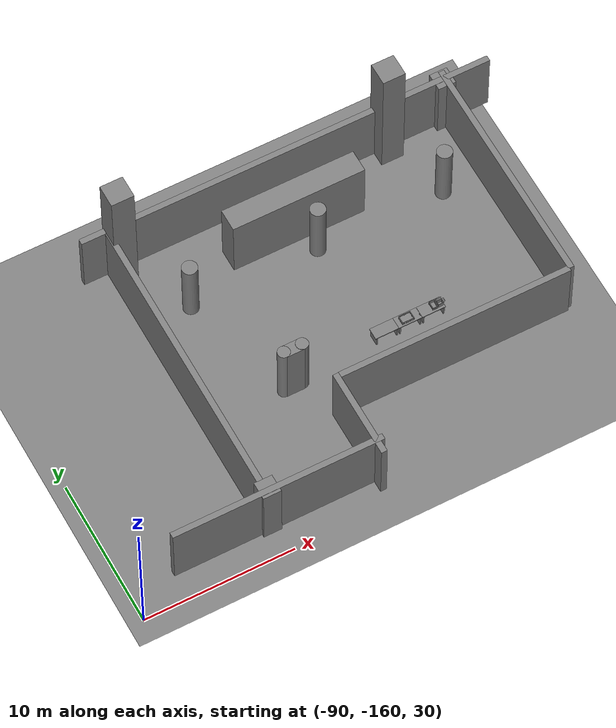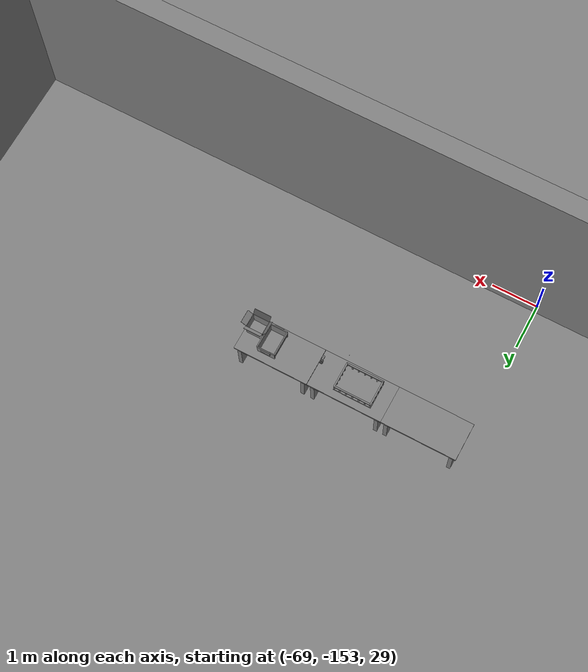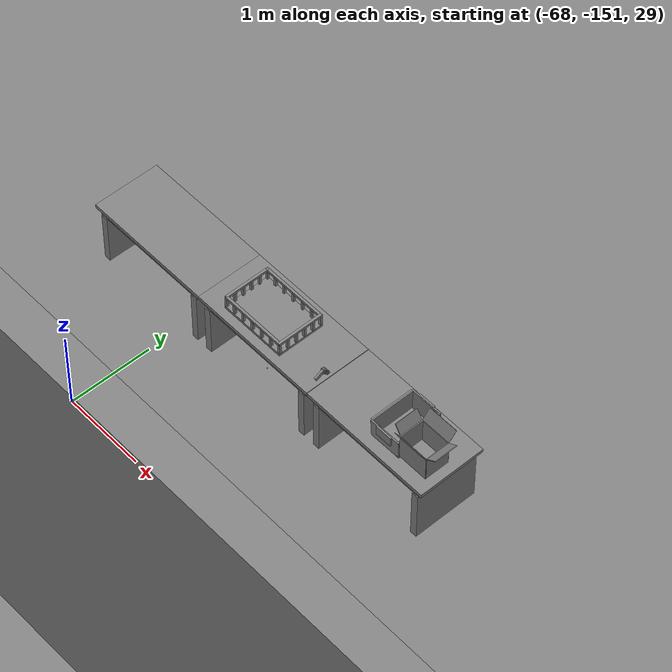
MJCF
<mujoco>
    <option gravity="0.000000000 0.000000000 -9.810000420" timestep="0.0049999999" integrator="implicitfast" density="1.225" viscosity="1.8000001e-05" noslip_iterations="10" iterations="100" sdf_iterations="50">
        <flag multiccd="disable"/>
    </option>
    <size memory="1000M"/>
    <compiler coordinate="local"/>
    <worldbody>
        <light cutoff="30" pos="0 1 1" dir="0 -1 -2"/>
        <light cutoff="30" pos="0 -1 1" dir="0 1 -2"/>
        <body pos="-64.866622925 -149.383972168 30.183746338" euler="89.999992371 89.999946594 0.000000000" name="openloong_gripper_2f85_fix_base_usda_bluebox_01">
            <geom contype="1" conaffinity="1" density="1000" type="box" material="" rgba="0.500000000 0.500000000 0.500000000 1.000000000" solimp="0.899999976 0.949999988 0.001000000" friction="1.000000000 0.005000000 0.000100000" solref="0.020000000 1.000000000" margin="0" condim="3" group="0" pos="0.276596069 0.187225342 0.000061035" quat="0.707107008 0.000077501 0.707106471 0.000077456" size="0.100000001 0.057999998 0.010000000" name="openloong_gripper_2f85_fix_base_usda_geom_52665D38_6ED9_464E_A63C_B9113DCB3281"/>
            <geom contype="1" conaffinity="1" density="1000" type="box" material="" rgba="0.500000000 0.500000000 0.500000000 1.000000000" solimp="0.899999976 0.949999988 0.001000000" friction="1.000000000 0.005000000 0.000100000" solref="0.020000000 1.000000000" margin="0" condim="3" group="0" pos="0.000000000 0.002883911 0.000000000" quat="1.000000000 0.000000000 0.000000000 0.000000000" size="0.254000008 0.003000000 0.172000006" name="openloong_gripper_2f85_fix_base_usda_geom_1125F259_DE69_4F67_8438_C8319A34BFF4"/>
            <geom contype="1" conaffinity="1" density="1000" type="box" material="" rgba="0.500000000 0.500000000 0.500000000 1.000000000" solimp="0.899999976 0.949999988 0.001000000" friction="1.000000000 0.005000000 0.000100000" solref="0.020000000 1.000000000" margin="0" condim="3" group="0" pos="0.000015259 0.124874115 0.173477173" quat="0.999796450 0.020176515 -0.000000015 0.000000030" size="0.259999990 0.119999997 0.007000000" name="openloong_gripper_2f85_fix_base_usda_geom_D6625337_C38E_456D_9C01_FB4EC2352ECF"/>
            <geom contype="1" conaffinity="1" density="1000" type="box" material="" rgba="0.500000000 0.500000000 0.500000000 1.000000000" solimp="0.899999976 0.949999988 0.001000000" friction="1.000000000 0.005000000 0.000100000" solref="0.020000000 1.000000000" margin="0" condim="3" group="0" pos="0.000015259 0.124874115 -0.173477173" quat="0.999796450 -0.020176545 -0.000000015 0.000000000" size="0.259999990 0.119999997 0.007000000" name="openloong_gripper_2f85_fix_base_usda_geom_3A82DDD0_76ED_4D56_80CC_02A8BD4BCC0A"/>
            <geom contype="1" conaffinity="1" density="1000" type="box" material="" rgba="0.500000000 0.500000000 0.500000000 1.000000000" solimp="0.899999976 0.949999988 0.001000000" friction="1.000000000 0.005000000 0.000100000" solref="0.020000000 1.000000000" margin="0" condim="3" group="0" pos="0.000015259 0.214012146 0.188980103" quat="0.999913096 0.013176724 0.000000015 0.000000000" size="0.259999990 0.029999999 0.012500000" name="openloong_gripper_2f85_fix_base_usda_geom_3C83AB9E_402A_4546_84A6_A42EF8570FB9"/>
            <geom contype="1" conaffinity="1" density="1000" type="box" material="" rgba="0.500000000 0.500000000 0.500000000 1.000000000" solimp="0.899999976 0.949999988 0.001000000" friction="1.000000000 0.005000000 0.000100000" solref="0.020000000 1.000000000" margin="0" condim="3" group="0" pos="-0.258346558 0.125289917 0.001876831" quat="0.702796996 -0.020792052 0.710783184 0.020769238" size="0.189999998 0.119999997 0.009000000" name="openloong_gripper_2f85_fix_base_usda_geom_66D8288B_E378_4265_AB0D_16A92438468F"/>
            <geom contype="1" conaffinity="1" density="1000" type="box" material="" rgba="0.500000000 0.500000000 0.500000000 1.000000000" solimp="0.899999976 0.949999988 0.001000000" friction="1.000000000 0.005000000 0.000100000" solref="0.020000000 1.000000000" margin="0" condim="3" group="0" pos="0.000015259 0.214012146 -0.188980103" quat="0.999913096 -0.013176769 0.000000030 0.000000015" size="0.259999990 0.029999999 0.012500000" name="openloong_gripper_2f85_fix_base_usda_geom_483AEBE0_918F_4CFF_B929_2F3B49FB0F31"/>
            <geom contype="1" conaffinity="1" density="1000" type="box" material="" rgba="0.500000000 0.500000000 0.500000000 1.000000000" solimp="0.899999976 0.949999988 0.001000000" friction="1.000000000 0.005000000 0.000100000" solref="0.020000000 1.000000000" margin="0" condim="3" group="0" pos="-0.276596069 0.187225342 0.000061035" quat="0.707106650 0.000077441 0.707106709 0.000077456" size="0.100000001 0.057999998 0.010000000" name="openloong_gripper_2f85_fix_base_usda_geom_841E7EEC_BFFC_41B8_86CE_6BA069710FFB"/>
            <geom contype="1" conaffinity="1" density="1000" type="box" material="" rgba="0.500000000 0.500000000 0.500000000 1.000000000" solimp="0.899999976 0.949999988 0.001000000" friction="1.000000000 0.005000000 0.000100000" solref="0.020000000 1.000000000" margin="0" condim="3" group="0" pos="0.258346558 0.125289917 0.001876831" quat="0.702851534 0.018856451 0.710823834 -0.019329429" size="0.189999998 0.119999997 0.009000000" name="openloong_gripper_2f85_fix_base_usda_geom_C8805E54_E434_43B0_A190_D594B5F55313"/>
            <freejoint name="openloong_gripper_2f85_fix_base_usda_bluebox_01_joint"/>
            <site size="0.005000000 0.005000000 0.005000000" rgba="0.500000000 0.500000000 0.500000000 1.000000000" pos="0.000000000 0.000000000 0.000000000" quat="0.999961913 0.008726534 0.000000000 0.000000000" group="0" type="sphere" name="openloong_gripper_2f85_fix_base_usda_bluebox_01site"/>
        </body>
        <body pos="-64.496299744 -149.491867065 30.235729218" euler="0.000000000 0.000000000 89.999946594" name="openloong_gripper_2f85_fix_base_usda_cardboardbox_01">
            <geom contype="1" conaffinity="1" density="1000" type="box" material="" rgba="0.500000000 0.500000000 0.500000000 1.000000000" solimp="0.899999976 0.949999988 0.001000000" friction="1.000000000 0.005000000 0.000100000" solref="0.020000000 1.000000000" margin="0" condim="3" group="0" pos="-0.003166199 -0.004086494 0.005052090" quat="1.000000000 0.000000000 0.000000000 0.000000000" size="0.142499998 0.177500010 0.005000000" name="openloong_gripper_2f85_fix_base_usda_geom_71AF2879_8F09_40EA_ADC1_2C541413A9D8"/>
            <geom contype="1" conaffinity="1" density="1000" type="box" material="" rgba="0.500000000 0.500000000 0.500000000 1.000000000" solimp="0.899999976 0.949999988 0.001000000" friction="1.000000000 0.005000000 0.000100000" solref="0.020000000 1.000000000" margin="0" condim="3" group="0" pos="-0.003166199 0.170316696 0.150570869" quat="1.000000000 0.000000000 0.000000000 0.000000000" size="0.142499998 0.005000000 0.149999991" name="openloong_gripper_2f85_fix_base_usda_geom_3CE75F2D_5053_4C83_91D6_190A2BB262B6"/>
            <geom contype="1" conaffinity="1" density="1000" type="box" material="" rgba="0.500000000 0.500000000 0.500000000 1.000000000" solimp="0.899999976 0.949999988 0.001000000" friction="1.000000000 0.005000000 0.000100000" solref="0.020000000 1.000000000" margin="0" condim="3" group="0" pos="-0.147399902 -0.005307198 0.150570869" quat="1.000000000 0.000000000 0.000000000 0.000000000" size="0.005000000 0.177500010 0.149999991" name="openloong_gripper_2f85_fix_base_usda_geom_5DA59672_D1AB_4320_9902_B8B181467B29"/>
            <geom contype="1" conaffinity="1" density="1000" type="box" material="" rgba="0.500000000 0.500000000 0.500000000 1.000000000" solimp="0.899999976 0.949999988 0.001000000" friction="1.000000000 0.005000000 0.000100000" solref="0.020000000 1.000000000" margin="0" condim="3" group="0" pos="0.140275955 -0.005307198 0.150570869" quat="1.000000000 0.000000000 0.000000000 0.000000000" size="0.005000000 0.177500010 0.149999991" name="openloong_gripper_2f85_fix_base_usda_geom_CE570D9E_535A_4FE3_A158_50073BD3DE22"/>
            <geom contype="1" conaffinity="1" density="1000" type="box" material="" rgba="0.500000000 0.500000000 0.500000000 1.000000000" solimp="0.899999976 0.949999988 0.001000000" friction="1.000000000 0.005000000 0.000100000" solref="0.020000000 1.000000000" margin="0" condim="3" group="0" pos="-0.003166199 -0.181550980 0.150570869" quat="1.000000000 0.000000000 0.000000000 0.000000000" size="0.142499998 0.005000000 0.149999991" name="openloong_gripper_2f85_fix_base_usda_geom_602EC679_5ACE_4219_BBB1_393B0ECDBEF6"/>
            <freejoint name="openloong_gripper_2f85_fix_base_usda_cardboardbox_01_joint"/>
            <site size="0.005000000 0.005000000 0.005000000" rgba="0.500000000 0.500000000 0.500000000 1.000000000" pos="0.000000000 0.000000000 0.000000000" quat="0.999961913 0.008726535 0.000000000 0.000000000" group="0" type="sphere" name="openloong_gripper_2f85_fix_base_usda_site_349CE9BA_B06F_4FAC_9589_7268E53826DA"/>
            <body pos="0.139160156 -0.004048347 0.301930904" euler="-179.999954224 49.383502960 179.999954224" name="openloong_gripper_2f85_fix_base_usda_A1_006">
                <geom contype="1" conaffinity="1" density="1000" type="box" material="" rgba="0.500000000 0.500000000 0.500000000 1.000000000" solimp="0.899999976 0.949999988 0.001000000" friction="1.000000000 0.005000000 0.000100000" solref="0.020000000 1.000000000" margin="0" condim="3" group="0" pos="-0.071587563 0.000009537 0.001745224" quat="0.999999881 0.000000000 0.000000000 0.000000000" size="0.071249999 0.179999992 0.002500000" name="openloong_gripper_2f85_fix_base_usda_geom_562759A8_4FDE_4429_9220_42B7DA44437F"/>
                <joint armature="0" stiffness="0.07" damping="0.0099999998" axis="0.000000 1.000000 0.000000" type="hinge" name="openloong_gripper_2f85_fix_base_usda_A1_006"/>
            </body>
            <body pos="-0.145902634 -0.004086494 0.301938057" euler="-180.000000000 -60.000011444 -180.000000000" name="openloong_gripper_2f85_fix_base_usda_A2_006">
                <geom contype="1" conaffinity="1" density="1000" type="box" material="" rgba="0.500000000 0.500000000 0.500000000 1.000000000" solimp="0.899999976 0.949999988 0.001000000" friction="1.000000000 0.005000000 0.000100000" solref="0.020000000 1.000000000" margin="0" condim="3" group="0" pos="0.071268082 0.000009537 0.002717972" quat="0.000002921 0.000000000 -0.000000030 0.999999881" size="0.071249999 0.179999992 0.002500000" name="openloong_gripper_2f85_fix_base_usda_geom_12ECE430_DD8E_4B37_9138_E0F5FC840234"/>
                <joint armature="0" stiffness="0.07" damping="0.0099999998" axis="0.000000 1.000000 0.000000" type="hinge" name="openloong_gripper_2f85_fix_base_usda_A2_006"/>
            </body>
            <body pos="-0.003385544 0.175991058 0.301930904" euler="-125.858116150 -0.000004561 0.000002331" name="openloong_gripper_2f85_fix_base_usda_B2_006">
                <geom contype="1" conaffinity="1" density="1000" type="box" material="" rgba="0.500000000 0.500000000 0.500000000 1.000000000" solimp="0.899999976 0.949999988 0.001000000" friction="1.000000000 0.005000000 0.000100000" solref="0.020000000 1.000000000" margin="0" condim="3" group="0" pos="0.000009537 -0.070939064 -0.002470016" quat="0.999614120 0.027776197 -0.000000015 0.000000030" size="0.137500003 0.064999998 0.005000000" name="openloong_gripper_2f85_fix_base_usda_geom_147416CB_8D0B_4A30_9D2D_2B8AD7E54598"/>
                <joint armature="0" stiffness="0.07" damping="0.0099999998" axis="1.000000 0.000000 0.000000" type="hinge" name="openloong_gripper_2f85_fix_base_usda_B2_006"/>
            </body>
            <body pos="-0.003385544 -0.184140205 0.301938057" euler="147.805557251 0.000000000 0.000000000" name="openloong_gripper_2f85_fix_base_usda_B1_006">
                <geom contype="1" conaffinity="1" density="1000" type="box" material="" rgba="0.500000000 0.500000000 0.500000000 1.000000000" solimp="0.899999976 0.949999988 0.001000000" friction="1.000000000 0.005000000 0.000100000" solref="0.020000000 1.000000000" margin="0" condim="3" group="0" pos="-0.000028610 0.070202351 -0.002703667" quat="0.999614179 -0.027776167 0.000000000 0.000000000" size="0.137500003 0.064999998 0.005000000" name="openloong_gripper_2f85_fix_base_usda_geom_40E1F8B4_C7EB_41B4_95E3_EFBE40E07E83"/>
                <joint armature="0" stiffness="0.07" damping="0.0099999998" axis="1.000000 0.000000 0.000000" type="hinge" name="openloong_gripper_2f85_fix_base_usda_B1_006"/>
            </body>
        </body>
        <body pos="-65.882858276 -149.481979370 30.229999542" euler="-64.487716675 0.000000000 0.000000000" name="openloong_gripper_2f85_fix_base_usda_Barcode">
            <geom contype="1" conaffinity="1" density="1000" type="box" material="" rgba="0.500000000 0.500000000 0.500000000 1.000000000" solimp="0.899999976 0.949999988 0.001000000" friction="1.000000000 0.005000000 0.000100000" solref="0.020000000 1.000000000" margin="0" condim="3" group="0" pos="0.000000000 0.013038635 0.001419067" quat="0.000000000 0.000000000 0.000000000 1.000000119" size="0.034000002 0.010000000 0.017999999" name="openloong_gripper_2f85_fix_base_usda_geom_185B43D7_5784_4D4F_8260_7F6184E7EB1C"/>
            <geom contype="1" conaffinity="1" density="1000" type="box" material="" rgba="0.500000000 0.500000000 0.500000000 1.000000000" solimp="0.899999976 0.949999988 0.001000000" friction="1.000000000 0.005000000 0.000100000" solref="0.020000000 1.000000000" margin="0" condim="3" group="0" pos="0.000000000 -0.035301208 -0.007095337" quat="0.000000000 0.000000000 -0.043619365 0.999048233" size="0.028999999 0.010000000 0.020000000" name="openloong_gripper_2f85_fix_base_usda_geom_A9B78FF1_77BE_4616_A562_52D9C9F28DD1"/>
            <geom contype="1" conaffinity="1" density="1000" type="box" material="" rgba="0.500000000 0.500000000 0.500000000 1.000000000" solimp="0.899999976 0.949999988 0.001000000" friction="1.000000000 0.005000000 0.000100000" solref="0.020000000 1.000000000" margin="0" condim="3" group="0" pos="0.000000000 -0.043411255 -0.011749268" quat="0.922262907 0.386563420 0.000000000 0.000000000" size="0.026000001 0.010000000 0.020000000" name="openloong_gripper_2f85_fix_base_usda_geom_9898CDB8_C767_46D6_94FF_F196B62A8884"/>
            <geom contype="1" conaffinity="1" density="1000" type="box" material="" rgba="0.500000000 0.500000000 0.500000000 1.000000000" solimp="0.899999976 0.949999988 0.001000000" friction="1.000000000 0.005000000 0.000100000" solref="0.020000000 1.000000000" margin="0" condim="3" group="0" pos="0.000000000 -0.016967773 -0.031860352" quat="0.000000000 0.000000000 0.000000000 1.000000119" size="0.008000000 0.010000000 0.013000000" name="openloong_gripper_2f85_fix_base_usda_geom_AF55CEB3_712B_48D2_AB9F_3FAEB5509D4D"/>
            <geom contype="1" conaffinity="1" density="1000" type="box" material="" rgba="0.500000000 0.500000000 0.500000000 1.000000000" solimp="0.899999976 0.949999988 0.001000000" friction="1.000000000 0.005000000 0.000100000" solref="0.020000000 1.000000000" margin="0" condim="3" group="0" pos="0.000000000 -0.001869202 0.000312805" quat="0.953716993 0.300705761 0.000000000 0.000000000" size="0.032000002 0.010000000 0.018999999" name="openloong_gripper_2f85_fix_base_usda_geom_222C8E57_E2FE_4B55_9FEF_8762A8913473"/>
            <geom contype="1" conaffinity="1" density="1000" type="box" material="" rgba="0.500000000 0.500000000 0.500000000 1.000000000" solimp="0.899999976 0.949999988 0.001000000" friction="1.000000000 0.005000000 0.000100000" solref="0.020000000 1.000000000" margin="0" condim="3" group="0" pos="0.000000000 -0.019531250 -0.003173828" quat="0.953716993 0.300705761 0.000000000 0.000000000" size="0.030999999 0.010000000 0.020000000" name="openloong_gripper_2f85_fix_base_usda_geom_51C09805_67A7_434A_B935_FECA7452277E"/>
            <geom contype="1" conaffinity="1" density="1000" type="box" material="" rgba="0.500000000 0.500000000 0.500000000 1.000000000" solimp="0.899999976 0.949999988 0.001000000" friction="1.000000000 0.005000000 0.000100000" solref="0.020000000 1.000000000" margin="0" condim="3" group="0" pos="0.000000000 -0.035301208 -0.007095337" quat="0.953716993 0.300705761 0.000000000 0.000000000" size="0.028999999 0.010000000 0.020000000" name="openloong_gripper_2f85_fix_base_usda_geom_AA95D05B_C6A4_4D4B_9F3D_8DA43BC84855"/>
            <geom contype="1" conaffinity="1" density="1000" type="box" material="" rgba="0.500000000 0.500000000 0.500000000 1.000000000" solimp="0.899999976 0.949999988 0.001000000" friction="1.000000000 0.005000000 0.000100000" solref="0.020000000 1.000000000" margin="0" condim="3" group="0" pos="0.000000000 -0.042617798 -0.071121216" quat="0.000000000 0.000000000 0.000000000 1.000000119" size="0.013000000 0.021000000 0.059999999" name="openloong_gripper_2f85_fix_base_usda_geom_48F8B89D_D28B_48DF_9FA2_99C257F03818"/>
            <freejoint name="openloong_gripper_2f85_fix_base_usda_Barcode_joint"/>
            <site size="0.005000000 0.005000000 0.005000000" rgba="0.500000000 0.500000000 0.500000000 1.000000000" pos="0.000000000 0.000000000 0.000000000" quat="1.000000000 0.000000000 0.000000000 0.000000000" group="0" type="sphere" name="openloong_gripper_2f85_fix_base_usda_Barcode_site"/>
        </body>
        <body pos="-66.745018005 -149.392349243 30.184000015" euler="0.000000000 0.000000000 89.999946594" name="[22329639609185]_Basket_01">
            <geom contype="1" conaffinity="1" density="1000" type="box" material="" rgba="0.500000000 0.500000000 0.500000000 1.000000000" solimp="0.899999976 0.949999988 0.001000000" friction="1.000000000 0.005000000 0.000100000" solref="0.020000000 1.000000000" margin="0" condim="3" group="0" pos="-0.052425385 0.389207840 0.089787483" quat="0.707107008 0.000000000 0.000000000 0.707106411" size="0.014249999 0.014249999 0.059999999" name="[22329639609185]_geom_ECC4810C_420F_4AAA_8BEF_A2FEAE68CB59"/>
            <geom contype="1" conaffinity="1" density="1000" type="box" material="" rgba="0.500000000 0.500000000 0.500000000 1.000000000" solimp="0.899999976 0.949999988 0.001000000" friction="1.000000000 0.005000000 0.000100000" solref="0.020000000 1.000000000" margin="0" condim="3" group="0" pos="0.264015198 -0.133043289 0.089787483" quat="0.707107008 0.000000000 0.000000000 0.707106411" size="0.014249999 0.014249999 0.059999999" name="[22329639609185]_geom_CB6824E0_658D_4003_BB69_72616DD50889"/>
            <geom contype="1" conaffinity="1" density="1000" type="box" material="" rgba="0.500000000 0.500000000 0.500000000 1.000000000" solimp="0.899999976 0.949999988 0.001000000" friction="1.000000000 0.005000000 0.000100000" solref="0.020000000 1.000000000" margin="0" condim="3" group="0" pos="-0.264015198 -0.265548706 0.089793205" quat="0.707107008 0.000000000 0.000000000 0.707106411" size="0.014249999 0.014249999 0.059999999" name="[22329639609185]_geom_05016A1E_0AAF_409B_A9CD_04EA2DF501DB"/>
            <geom contype="1" conaffinity="1" density="1000" type="box" material="" rgba="0.500000000 0.500000000 0.500000000 1.000000000" solimp="0.899999976 0.949999988 0.001000000" friction="1.000000000 0.005000000 0.000100000" solref="0.020000000 1.000000000" margin="0" condim="3" group="0" pos="-0.160263062 -0.389322281 0.089793205" quat="0.707107008 0.000000000 0.000000000 0.707106411" size="0.014249999 0.014249999 0.059999999" name="[22329639609185]_geom_701C2421_F14F_4570_B795_5FC907CEC3E9"/>
            <geom contype="1" conaffinity="1" density="1000" type="box" material="" rgba="0.500000000 0.500000000 0.500000000 1.000000000" solimp="0.899999976 0.949999988 0.001000000" friction="1.000000000 0.005000000 0.000100000" solref="0.020000000 1.000000000" margin="0" condim="3" group="0" pos="0.162265778 -0.389322281 0.089787483" quat="0.707107008 0.000000000 0.000000000 0.707106411" size="0.014249999 0.014249999 0.059999999" name="[22329639609185]_geom_A403FD0C_A978_41B4_9B32_03F5E4BD2D9A"/>
            <geom contype="1" conaffinity="1" density="1000" type="box" material="" rgba="0.500000000 0.500000000 0.500000000 1.000000000" solimp="0.899999976 0.949999988 0.001000000" friction="1.000000000 0.005000000 0.000100000" solref="0.020000000 1.000000000" margin="0" condim="3" group="0" pos="0.264015198 0.389207840 0.089787483" quat="0.707107008 0.000000000 0.000000000 0.707106411" size="0.014249999 0.014249999 0.059999999" name="[22329639609185]_geom_A337F30F_536E_4409_9751_AA49F6EA7E83"/>
            <geom contype="1" conaffinity="1" density="1000" type="box" material="" rgba="0.500000000 0.500000000 0.500000000 1.000000000" solimp="0.899999976 0.949999988 0.001000000" friction="1.000000000 0.005000000 0.000100000" solref="0.020000000 1.000000000" margin="0" condim="3" group="0" pos="-0.264015198 -0.133043289 0.089793205" quat="0.707107008 0.000000000 0.000000000 0.707106411" size="0.014249999 0.014249999 0.059999999" name="[22329639609185]_geom_7C5A1643_86E5_454E_861C_BAD032B55938"/>
            <geom contype="1" conaffinity="1" density="1000" type="box" material="" rgba="0.500000000 0.500000000 0.500000000 1.000000000" solimp="0.899999976 0.949999988 0.001000000" friction="1.000000000 0.005000000 0.000100000" solref="0.020000000 1.000000000" margin="0" condim="3" group="0" pos="-0.264026642 0.269256592 0.089793205" quat="0.707107008 0.000000000 0.000000000 0.707106411" size="0.014249999 0.014249999 0.059999999" name="[22329639609185]_geom_8EA4921D_600A_4B9A_8E66_D893D99C7F96"/>
            <geom contype="1" conaffinity="1" density="1000" type="box" material="" rgba="0.500000000 0.500000000 0.500000000 1.000000000" solimp="0.899999976 0.949999988 0.001000000" friction="1.000000000 0.005000000 0.000100000" solref="0.020000000 1.000000000" margin="0" condim="3" group="0" pos="0.054462433 0.389207840 0.089787483" quat="0.707107008 0.000000000 0.000000000 0.707106411" size="0.014249999 0.014249999 0.059999999" name="[22329639609185]_geom_E459053C_C652_4325_A2FD_048729333B64"/>
            <geom contype="1" conaffinity="1" density="1000" type="box" material="" rgba="0.500000000 0.500000000 0.500000000 1.000000000" solimp="0.899999976 0.949999988 0.001000000" friction="1.000000000 0.005000000 0.000100000" solref="0.020000000 1.000000000" margin="0" condim="3" group="0" pos="0.054462433 -0.389322281 0.089787483" quat="0.707107008 0.000000000 0.000000000 0.707106411" size="0.014249999 0.014249999 0.059999999" name="[22329639609185]_geom_4A6C8C18_84AD_44F1_A90E_8ED0B048D726"/>
            <geom contype="1" conaffinity="1" density="1000" type="box" material="" rgba="0.500000000 0.500000000 0.500000000 1.000000000" solimp="0.899999976 0.949999988 0.001000000" friction="1.000000000 0.005000000 0.000100000" solref="0.020000000 1.000000000" margin="0" condim="3" group="0" pos="0.264015198 0.269256592 0.089793205" quat="0.707107008 0.000000000 0.000000000 0.707106411" size="0.014249999 0.014249999 0.059999999" name="[22329639609185]_geom_58B750FC_7078_46E3_BD8C_800D4B283CBF"/>
            <geom contype="1" conaffinity="1" density="1000" type="box" material="" rgba="0.500000000 0.500000000 0.500000000 1.000000000" solimp="0.899999976 0.949999988 0.001000000" friction="1.000000000 0.005000000 0.000100000" solref="0.020000000 1.000000000" margin="0" condim="3" group="0" pos="0.264015198 -0.389322281 0.089787483" quat="0.707107008 0.000000000 0.000000000 0.707106411" size="0.014249999 0.014249999 0.059999999" name="[22329639609185]_geom_2F1594F2_D1BD_4C3B_A271_113341B77F41"/>
            <geom contype="1" conaffinity="1" density="1000" type="box" material="" rgba="0.500000000 0.500000000 0.500000000 1.000000000" solimp="0.899999976 0.949999988 0.001000000" friction="1.000000000 0.005000000 0.000100000" solref="0.020000000 1.000000000" margin="0" condim="3" group="0" pos="0.000000000 0.000000000 0.015998840" quat="0.707107008 0.000000000 0.000000000 0.707106411" size="0.403499991 0.279000014 0.015750000" name="[22329639609185]_geom_547701C9_55F5_4581_A7FB_091166C3D16C"/>
            <geom contype="1" conaffinity="1" density="1000" type="box" material="" rgba="0.500000000 0.500000000 0.500000000 1.000000000" solimp="0.899999976 0.949999988 0.001000000" friction="1.000000000 0.005000000 0.000100000" solref="0.020000000 1.000000000" margin="0" condim="3" group="0" pos="0.000000000 -0.389476776 0.163619041" quat="0.707107008 0.000000000 0.000000000 0.707106411" size="0.015000000 0.277500004 0.015750000" name="[22329639609185]_geom_4ACB1872_65BA_4828_9133_10023BED6151"/>
            <geom contype="1" conaffinity="1" density="1000" type="box" material="" rgba="0.500000000 0.500000000 0.500000000 1.000000000" solimp="0.899999976 0.949999988 0.001000000" friction="1.000000000 0.005000000 0.000100000" solref="0.020000000 1.000000000" margin="0" condim="3" group="0" pos="0.162265778 0.389207840 0.089787483" quat="0.707107008 0.000000000 0.000000000 0.707106411" size="0.014249999 0.014249999 0.059999999" name="[22329639609185]_geom_05F819C1_8970_446B_9F14_E703A25B7BC8"/>
            <geom contype="1" conaffinity="1" density="1000" type="box" material="" rgba="0.500000000 0.500000000 0.500000000 1.000000000" solimp="0.899999976 0.949999988 0.001000000" friction="1.000000000 0.005000000 0.000100000" solref="0.020000000 1.000000000" margin="0" condim="3" group="0" pos="0.000000000 0.389471054 0.163619041" quat="0.707107008 0.000000000 0.000000000 0.707106411" size="0.015000000 0.277500004 0.015750000" name="[22329639609185]_geom_DD8AD477_0701_404B_8329_A0D9FD409042"/>
            <geom contype="1" conaffinity="1" density="1000" type="box" material="" rgba="0.500000000 0.500000000 0.500000000 1.000000000" solimp="0.899999976 0.949999988 0.001000000" friction="1.000000000 0.005000000 0.000100000" solref="0.020000000 1.000000000" margin="0" condim="3" group="0" pos="-0.263511658 0.000000000 0.163619041" quat="0.707107008 0.000000000 0.000000000 0.707106411" size="0.403499991 0.015000000 0.015750000" name="[22329639609185]_geom_5381DF4D_C44B_450A_87B9_1C42DEFE37AF"/>
            <geom contype="1" conaffinity="1" density="1000" type="box" material="" rgba="0.500000000 0.500000000 0.500000000 1.000000000" solimp="0.899999976 0.949999988 0.001000000" friction="1.000000000 0.005000000 0.000100000" solref="0.020000000 1.000000000" margin="0" condim="3" group="0" pos="-0.264015198 0.141334534 0.089793205" quat="0.707107008 0.000000000 0.000000000 0.707106411" size="0.014249999 0.014249999 0.059999999" name="[22329639609185]_geom_C64458A4_B12C_4E2E_B7F4_B384FC692893"/>
            <geom contype="1" conaffinity="1" density="1000" type="box" material="" rgba="0.500000000 0.500000000 0.500000000 1.000000000" solimp="0.899999976 0.949999988 0.001000000" friction="1.000000000 0.005000000 0.000100000" solref="0.020000000 1.000000000" margin="0" condim="3" group="0" pos="0.264015198 -0.265548706 0.089787483" quat="0.707107008 0.000000000 0.000000000 0.707106411" size="0.014249999 0.014249999 0.059999999" name="[22329639609185]_geom_4D15DC84_A3CE_4FB2_8B68_9AAEEE34D79B"/>
            <geom contype="1" conaffinity="1" density="1000" type="box" material="" rgba="0.500000000 0.500000000 0.500000000 1.000000000" solimp="0.899999976 0.949999988 0.001000000" friction="1.000000000 0.005000000 0.000100000" solref="0.020000000 1.000000000" margin="0" condim="3" group="0" pos="-0.160263062 0.389207840 0.089787483" quat="0.707107008 0.000000000 0.000000000 0.707106411" size="0.014249999 0.014249999 0.059999999" name="[22329639609185]_geom_EA19DEBD_32E5_48AA_965E_D0E8FF3084DC"/>
            <geom contype="1" conaffinity="1" density="1000" type="box" material="" rgba="0.500000000 0.500000000 0.500000000 1.000000000" solimp="0.899999976 0.949999988 0.001000000" friction="1.000000000 0.005000000 0.000100000" solref="0.020000000 1.000000000" margin="0" condim="3" group="0" pos="-0.052425385 -0.389322281 0.089787483" quat="0.707107008 0.000000000 0.000000000 0.707106411" size="0.014249999 0.014249999 0.059999999" name="[22329639609185]_geom_32DEAD28_5FC9_4196_818F_968EBB525B5E"/>
            <geom contype="1" conaffinity="1" density="1000" type="box" material="" rgba="0.500000000 0.500000000 0.500000000 1.000000000" solimp="0.899999976 0.949999988 0.001000000" friction="1.000000000 0.005000000 0.000100000" solref="0.020000000 1.000000000" margin="0" condim="3" group="0" pos="-0.264026642 -0.389322281 0.089793205" quat="0.707107008 0.000000000 0.000000000 0.707106411" size="0.014249999 0.014249999 0.059999999" name="[22329639609185]_geom_74F2D9DC_7CD1_44C9_987D_8C0B2707D0E4"/>
            <geom contype="1" conaffinity="1" density="1000" type="box" material="" rgba="0.500000000 0.500000000 0.500000000 1.000000000" solimp="0.899999976 0.949999988 0.001000000" friction="1.000000000 0.005000000 0.000100000" solref="0.020000000 1.000000000" margin="0" condim="3" group="0" pos="0.264015198 0.141334534 0.089787483" quat="0.707107008 0.000000000 0.000000000 0.707106411" size="0.014249999 0.014249999 0.059999999" name="[22329639609185]_geom_B9F50EB8_611E_4A5E_9954_A9CF590482C3"/>
            <geom contype="1" conaffinity="1" density="1000" type="box" material="" rgba="0.500000000 0.500000000 0.500000000 1.000000000" solimp="0.899999976 0.949999988 0.001000000" friction="1.000000000 0.005000000 0.000100000" solref="0.020000000 1.000000000" margin="0" condim="3" group="0" pos="-0.264015198 0.389207840 0.089793205" quat="0.707107008 0.000000000 0.000000000 0.707106411" size="0.014249999 0.014249999 0.059999999" name="[22329639609185]_geom_2F48C598_364F_48F8_9F6D_65BDD5EB6CB9"/>
            <geom contype="1" conaffinity="1" density="1000" type="box" material="" rgba="0.500000000 0.500000000 0.500000000 1.000000000" solimp="0.899999976 0.949999988 0.001000000" friction="1.000000000 0.005000000 0.000100000" solref="0.020000000 1.000000000" margin="0" condim="3" group="0" pos="0.264015198 0.004480362 0.089787483" quat="0.707107008 0.000000000 0.000000000 0.707106411" size="0.014249999 0.014249999 0.059999999" name="[22329639609185]_geom_582ADF17_1AAB_4DD2_A5BA_007723DF2E7D"/>
            <geom contype="1" conaffinity="1" density="1000" type="box" material="" rgba="0.500000000 0.500000000 0.500000000 1.000000000" solimp="0.899999976 0.949999988 0.001000000" friction="1.000000000 0.005000000 0.000100000" solref="0.020000000 1.000000000" margin="0" condim="3" group="0" pos="0.263694763 -0.000011444 0.163619041" quat="0.707107008 0.000000000 0.000000000 0.707106411" size="0.403499991 0.015000000 0.015750000" name="[22329639609185]_geom_FF443BC1_D198_4BF2_BA9E_C5F0FC8D855B"/>
            <geom contype="1" conaffinity="1" density="1000" type="box" material="" rgba="0.500000000 0.500000000 0.500000000 1.000000000" solimp="0.899999976 0.949999988 0.001000000" friction="1.000000000 0.005000000 0.000100000" solref="0.020000000 1.000000000" margin="0" condim="3" group="0" pos="-0.264015198 0.004480362 0.089793205" quat="0.707107008 0.000000000 0.000000000 0.707106411" size="0.014249999 0.014249999 0.059999999" name="[22329639609185]_geom_B6A167B4_605F_462E_B2BF_62D90B5A2F27"/>
            <freejoint name="[22329639609185]_joint_E08B3287_308B_404C_A4F2_2498B3018362"/>
        </body>
        <body pos="0.000000000 0.000000000 0.000000000" euler="0.000000000 0.000000000 0.000000000" name="Static Objects_Static Objects">
            <geom contype="1" conaffinity="1" density="1000" type="box" material="" rgba="0.500000000 0.500000000 0.500000000 1.000000000" solimp="0.899999976 0.949999988 0.001000000" friction="1.000000000 0.005000000 0.000100000" solref="0.020000000 1.000000000" margin="0" condim="3" group="0" pos="-67.544113159 -149.365814209 29.727830887" quat="0.500000417 0.499999970 0.499999553 0.499999970" size="0.381000012 0.319999993 0.041000001" name="Static Objects_geom_F0B4446B_1135_437E_98A1_7CE5B31B78CB"/>
            <geom contype="1" conaffinity="1" density="1000" type="box" material="" rgba="0.500000000 0.500000000 0.500000000 1.000000000" solimp="0.899999976 0.949999988 0.001000000" friction="1.000000000 0.005000000 0.000100000" solref="0.020000000 1.000000000" margin="0" condim="3" group="0" pos="-68.239501953 -149.365814209 30.086868286" quat="0.500000417 0.499999970 0.499999553 0.499999970" size="0.370999992 0.039500002 0.745000005" name="Static Objects_geom_052A7545_F807_4956_BD7B_BBC04530C058"/>
            <geom contype="1" conaffinity="1" density="1000" type="box" material="" rgba="0.500000000 0.500000000 0.500000000 1.000000000" solimp="0.899999976 0.949999988 0.001000000" friction="1.000000000 0.005000000 0.000100000" solref="0.020000000 1.000000000" margin="0" condim="3" group="0" pos="-68.239501953 -149.365814209 30.147235870" quat="0.500000417 0.499999970 0.499999553 0.499999970" size="0.400000006 0.022000000 0.800000012" name="Static Objects_geom_8B57F41C_E9E9_4C7C_84A4_4D12D0982F47"/>
            <geom contype="1" conaffinity="1" density="1000" type="box" material="" rgba="0.500000000 0.500000000 0.500000000 1.000000000" solimp="0.899999976 0.949999988 0.001000000" friction="1.000000000 0.005000000 0.000100000" solref="0.020000000 1.000000000" margin="0" condim="3" group="0" pos="-68.934890747 -149.365814209 29.727830887" quat="0.500000417 0.499999970 0.499999553 0.499999970" size="0.381000012 0.319999993 0.041000001" name="Static Objects_geom_908FF109_8612_419F_AB81_34E65F19E2DE"/>
            <geom contype="1" conaffinity="1" density="1000" type="box" material="" rgba="0.500000000 0.500000000 0.500000000 1.000000000" solimp="0.899999976 0.949999988 0.001000000" friction="1.000000000 0.005000000 0.000100000" solref="0.020000000 1.000000000" margin="0" condim="3" group="0" pos="-68.239501953 -149.365814209 29.561563492" quat="0.500000417 0.499999970 0.499999553 0.499999970" size="0.020000000 0.022000000 0.660000026" name="Static Objects_geom_6C350E50_BA2F_409D_9E16_D09DC17F0635"/>
            <geom contype="1" conaffinity="1" density="1000" type="box" material="" rgba="0.500000000 0.500000000 0.500000000 1.000000000" solimp="0.899999976 0.949999988 0.001000000" friction="1.000000000 0.005000000 0.000100000" solref="0.020000000 1.000000000" margin="0" condim="3" group="0" pos="-65.945671082 -149.365814209 29.727830887" quat="0.500000417 0.499999970 0.499999553 0.499999970" size="0.381000012 0.319999993 0.041000001" name="Static Objects_geom_2F2835F8_3B28_488C_B858_CB744A7E4CCD"/>
            <geom contype="1" conaffinity="1" density="1000" type="box" material="" rgba="0.500000000 0.500000000 0.500000000 1.000000000" solimp="0.899999976 0.949999988 0.001000000" friction="1.000000000 0.005000000 0.000100000" solref="0.020000000 1.000000000" margin="0" condim="3" group="0" pos="-66.641059875 -149.365814209 30.086868286" quat="0.500000417 0.499999970 0.499999553 0.499999970" size="0.370999992 0.039500002 0.745000005" name="Static Objects_geom_AF186154_0B4B_4518_9B1B_C35BB18A7CED"/>
            <geom contype="1" conaffinity="1" density="1000" type="box" material="" rgba="0.500000000 0.500000000 0.500000000 1.000000000" solimp="0.899999976 0.949999988 0.001000000" friction="1.000000000 0.005000000 0.000100000" solref="0.020000000 1.000000000" margin="0" condim="3" group="0" pos="-66.641059875 -149.365814209 30.147235870" quat="0.500000417 0.499999970 0.499999553 0.499999970" size="0.400000006 0.022000000 0.800000012" name="Static Objects_geom_8268D16D_4A82_4CA7_AA20_7E22D5687404"/>
            <geom contype="1" conaffinity="1" density="1000" type="box" material="" rgba="0.500000000 0.500000000 0.500000000 1.000000000" solimp="0.899999976 0.949999988 0.001000000" friction="1.000000000 0.005000000 0.000100000" solref="0.020000000 1.000000000" margin="0" condim="3" group="0" pos="-67.336448669 -149.365814209 29.727830887" quat="0.500000417 0.499999970 0.499999553 0.499999970" size="0.381000012 0.319999993 0.041000001" name="Static Objects_geom_6A02DC7F_5785_499E_BE40_BE530A14D35E"/>
            <geom contype="1" conaffinity="1" density="1000" type="box" material="" rgba="0.500000000 0.500000000 0.500000000 1.000000000" solimp="0.899999976 0.949999988 0.001000000" friction="1.000000000 0.005000000 0.000100000" solref="0.020000000 1.000000000" margin="0" condim="3" group="0" pos="-66.641059875 -149.365814209 29.561563492" quat="0.500000417 0.499999970 0.499999553 0.499999970" size="0.020000000 0.022000000 0.660000026" name="Static Objects_geom_D1E2EACB_A574_4F45_9310_5338C8F4D88E"/>
            <geom contype="1" conaffinity="1" density="1000" type="box" material="" rgba="0.500000000 0.500000000 0.500000000 1.000000000" solimp="0.899999976 0.949999988 0.001000000" friction="1.000000000 0.005000000 0.000100000" solref="0.020000000 1.000000000" margin="0" condim="3" group="0" pos="-64.338577271 -149.365814209 29.727830887" quat="0.500000417 0.499999970 0.499999553 0.499999970" size="0.381000012 0.319999993 0.041000001" name="Static Objects_geom_69A740BE_51A2_42DA_AEE3_F2CBDB3569E4"/>
            <geom contype="1" conaffinity="1" density="1000" type="box" material="" rgba="0.500000000 0.500000000 0.500000000 1.000000000" solimp="0.899999976 0.949999988 0.001000000" friction="1.000000000 0.005000000 0.000100000" solref="0.020000000 1.000000000" margin="0" condim="3" group="0" pos="-65.033966064 -149.365814209 30.086868286" quat="0.500000417 0.499999970 0.499999553 0.499999970" size="0.370999992 0.039500002 0.745000005" name="Static Objects_geom_49A4FC43_D8FF_4125_BDE6_5CC6EE91976B"/>
            <geom contype="1" conaffinity="1" density="1000" type="box" material="" rgba="0.500000000 0.500000000 0.500000000 1.000000000" solimp="0.899999976 0.949999988 0.001000000" friction="1.000000000 0.005000000 0.000100000" solref="0.020000000 1.000000000" margin="0" condim="3" group="0" pos="-65.033966064 -149.365814209 30.147235870" quat="0.500000417 0.499999970 0.499999553 0.499999970" size="0.400000006 0.022000000 0.800000012" name="Static Objects_geom_5F6E7DE9_2B2F_4A50_BDC0_4D1A0BC16F21"/>
            <geom contype="1" conaffinity="1" density="1000" type="box" material="" rgba="0.500000000 0.500000000 0.500000000 1.000000000" solimp="0.899999976 0.949999988 0.001000000" friction="1.000000000 0.005000000 0.000100000" solref="0.020000000 1.000000000" margin="0" condim="3" group="0" pos="-65.729354858 -149.365814209 29.727830887" quat="0.500000417 0.499999970 0.499999553 0.499999970" size="0.381000012 0.319999993 0.041000001" name="Static Objects_geom_7F33DA65_3351_44D5_93F7_C426E8CBA674"/>
            <geom contype="1" conaffinity="1" density="1000" type="box" material="" rgba="0.500000000 0.500000000 0.500000000 1.000000000" solimp="0.899999976 0.949999988 0.001000000" friction="1.000000000 0.005000000 0.000100000" solref="0.020000000 1.000000000" margin="0" condim="3" group="0" pos="-65.033966064 -149.365814209 29.561563492" quat="0.500000417 0.499999970 0.499999553 0.499999970" size="0.020000000 0.022000000 0.660000026" name="Static Objects_geom_9A21F56C_6B05_4324_A9E3_EBCCBAD95767"/>
            <geom contype="1" conaffinity="1" density="1000" type="box" material="" rgba="0.500000000 0.500000000 0.500000000 1.000000000" solimp="0.899999976 0.949999988 0.001000000" friction="1.000000000 0.005000000 0.000100000" solref="0.020000000 1.000000000" margin="0" condim="3" group="0" pos="-61.754566193 -137.853729248 33.906845093" quat="0.707107067 0.000000000 0.000000000 0.707106471" size="0.759999990 0.759999990 4.500000000" name="Static Objects_geom_F3E7B71E_6090_4D4F_A5A1_63CCA1B5762C"/>
            <geom contype="1" conaffinity="1" density="1000" type="box" material="" rgba="0.500000000 0.500000000 0.500000000 1.000000000" solimp="0.899999976 0.949999988 0.001000000" friction="1.000000000 0.005000000 0.000100000" solref="0.020000000 1.000000000" margin="0" condim="3" group="0" pos="-57.511135101 -144.927108765 31.707921982" quat="1.000000000 0.000000000 0.000000000 0.000000000" size="0.200000003 8.000000000 2.299999952" name="Static Objects_geom_E65D1AE4_3DB6_4351_99ED_263EA13138BB"/>
            <geom contype="1" conaffinity="1" density="1000" type="box" material="" rgba="0.500000000 0.500000000 0.500000000 1.000000000" solimp="0.899999976 0.949999988 0.001000000" friction="1.000000000 0.005000000 0.000100000" solref="0.020000000 1.000000000" margin="0" condim="3" group="0" pos="-80.517646790 -157.574050903 31.688196182" quat="0.707107067 0.000000000 0.000000000 0.707106471" size="0.600000024 0.600000024 2.299999952" name="Static Objects_geom_023CA514_AB5A_4039_9579_73BB80CB3B0C"/>
            <geom contype="1" conaffinity="1" density="1000" type="box" material="" rgba="0.500000000 0.500000000 0.500000000 1.000000000" solimp="0.899999976 0.949999988 0.001000000" friction="1.000000000 0.005000000 0.000100000" solref="0.020000000 1.000000000" margin="0" condim="3" group="0" pos="-80.711044312 -147.414932251 31.666158676" quat="1.000000000 0.000000000 0.000000000 0.000000000" size="0.200000003 10.000000000 2.299999952" name="Static Objects_geom_B3C558F2_100B_4CE1_8605_94EA79F20F71"/>
            <geom contype="1" conaffinity="1" density="1000" type="box" material="" rgba="0.500000000 0.500000000 0.500000000 1.000000000" solimp="0.899999976 0.949999988 0.001000000" friction="1.000000000 0.005000000 0.000100000" solref="0.020000000 1.000000000" margin="0" condim="3" group="0" pos="-57.687217712 -137.434692383 31.688196182" quat="0.707107067 0.000000000 0.000000000 0.707106471" size="0.600000024 0.600000024 2.299999952" name="Static Objects_geom_544E2A81_182B_4C6B_AFBB_3167DFA6969C"/>
            <geom contype="1" conaffinity="1" density="1000" type="box" material="" rgba="0.500000000 0.500000000 0.500000000 1.000000000" solimp="0.899999976 0.949999988 0.001000000" friction="1.000000000 0.005000000 0.000100000" solref="0.020000000 1.000000000" margin="0" condim="3" group="0" pos="-69.537033081 -140.263229370 31.714921951" quat="0.707107067 0.000000000 0.000000000 0.707106471" size="0.759999990 4.500000000 2.299999952" name="Static Objects_geom_884B2BD8_17ED_48F3_B7BF_BC34BF351911"/>
            <geom contype="1" conaffinity="1" density="1000" type="box" material="" rgba="0.500000000 0.500000000 0.500000000 1.000000000" solimp="0.899999976 0.949999988 0.001000000" friction="1.000000000 0.005000000 0.000100000" solref="0.020000000 1.000000000" margin="0" condim="3" group="0" pos="-80.073638916 -137.853713989 33.906845093" quat="0.707107067 0.000000000 0.000000000 0.707106471" size="0.759999990 0.759999990 4.500000000" name="Static Objects_geom_66BC65E3_6863_4145_842A_78482B2FC730"/>
            <geom contype="1" conaffinity="1" density="1000" type="box" material="" rgba="0.500000000 0.500000000 0.500000000 1.000000000" solimp="0.899999976 0.949999988 0.001000000" friction="1.000000000 0.005000000 0.000100000" solref="0.020000000 1.000000000" margin="0" condim="3" group="0" pos="-73.406707764 -155.734664917 31.707921982" quat="1.000000000 0.000000000 0.000000000 0.000000000" size="0.200000003 3.000000000 2.299999952" name="Static Objects_geom_920504B9_CA54_455A_9009_6580E126800E"/>
            <geom contype="1" conaffinity="1" density="1000" type="box" material="" rgba="0.500000000 0.500000000 0.500000000 1.000000000" solimp="0.899999976 0.949999988 0.001000000" friction="1.000000000 0.005000000 0.000100000" solref="0.020000000 1.000000000" margin="0" condim="3" group="0" pos="-68.497543335 -137.448257446 31.707921982" quat="0.707107067 0.000000000 0.000000000 0.707106471" size="0.200000003 14.000000000 2.299999952" name="Static Objects_geom_1E010DE1_0794_4AE0_B9C9_57129725E9DF"/>
            <geom contype="1" conaffinity="1" density="1000" type="cylinder" material="" rgba="0.500000000 0.500000000 0.500000000 1.000000000" solimp="0.899999976 0.949999988 0.001000000" friction="1.000000000 0.005000000 0.000100000" solref="0.020000000 1.000000000" margin="0" condim="3" group="0" pos="-68.868522644 -142.134506226 31.711090088" quat="0.707107067 0.000000000 0.000000000 0.707106471" size="0.509999990 2.299999952 1.000000000" name="Static Objects_geom_DA90C8AC_1C52_49B0_98B0_22945CC59A33"/>
            <geom contype="1" conaffinity="1" density="1000" type="plane" material="" rgba="0.500000000 0.500000000 0.500000000 1.000000000" solimp="0.899999976 0.949999988 0.001000000" friction="1.000000000 0.005000000 0.000100000" solref="0.020000000 1.000000000" margin="0" condim="3" group="0" pos="-72.873703003 -147.131927490 29.409669876" quat="1.000000000 0.000000000 0.000000000 0.000000000" size="18.000000000 14.000000000 1.000000000" name="Static Objects_geom_363B18B2_8E1B_408F_BF1F_F630431136B3"/>
            <geom contype="1" conaffinity="1" density="1000" type="box" material="" rgba="0.500000000 0.500000000 0.500000000 1.000000000" solimp="0.899999976 0.949999988 0.001000000" friction="1.000000000 0.005000000 0.000100000" solref="0.020000000 1.000000000" margin="0" condim="3" group="0" pos="-79.943580627 -157.782272339 31.707921982" quat="0.707107067 0.000000000 0.000000000 0.707106471" size="0.200000003 7.000000000 2.299999952" name="Static Objects_geom_A5B80C69_4808_4F6B_9DFC_C9FB70DF1925"/>
            <geom contype="1" conaffinity="1" density="1000" type="box" material="" rgba="0.500000000 0.500000000 0.500000000 1.000000000" solimp="0.899999976 0.949999988 0.001000000" friction="1.000000000 0.005000000 0.000100000" solref="0.020000000 1.000000000" margin="0" condim="3" group="0" pos="-65.421028137 -152.903442383 31.707921982" quat="0.707107067 0.000000000 0.000000000 0.707106471" size="0.200000003 7.800000191 2.299999952" name="Static Objects_geom_F306054C_3C18_4887_9B69_4219F1C18CDA"/>
            <geom contype="1" conaffinity="1" density="1000" type="box" material="" rgba="0.500000000 0.500000000 0.500000000 1.000000000" solimp="0.899999976 0.949999988 0.001000000" friction="1.000000000 0.005000000 0.000100000" solref="0.020000000 1.000000000" margin="0" condim="3" group="0" pos="-74.776908875 -149.964416504 31.688196182" quat="1.000000000 0.000000000 0.000000000 0.000000000" size="0.600000024 0.409999996 2.299999952" name="Static Objects_geom_83527581_FCD8_44A2_BE6F_35EB1821026D"/>
            <geom contype="1" conaffinity="1" density="1000" type="cylinder" material="" rgba="0.500000000 0.500000000 0.500000000 1.000000000" solimp="0.899999976 0.949999988 0.001000000" friction="1.000000000 0.005000000 0.000100000" solref="0.020000000 1.000000000" margin="0" condim="3" group="0" pos="-60.161884308 -142.134506226 31.711090088" quat="0.707107067 0.000000000 0.000000000 0.707106471" size="0.509999990 2.299999952 1.000000000" name="Static Objects_geom_1F2C4C38_2A0C_48A9_81B8_819E4CFE83DC"/>
            <geom contype="1" conaffinity="1" density="1000" type="cylinder" material="" rgba="0.500000000 0.500000000 0.500000000 1.000000000" solimp="0.899999976 0.949999988 0.001000000" friction="1.000000000 0.005000000 0.000100000" solref="0.020000000 1.000000000" margin="0" condim="3" group="0" pos="-75.382453918 -149.963455200 31.711090088" quat="0.707107067 0.000000000 0.000000000 0.707106471" size="0.409999996 2.299999952 1.000000000" name="Static Objects_geom_169D331C_F437_497A_A5E3_52AD73FFA175"/>
            <geom contype="1" conaffinity="1" density="1000" type="cylinder" material="" rgba="0.500000000 0.500000000 0.500000000 1.000000000" solimp="0.899999976 0.949999988 0.001000000" friction="1.000000000 0.005000000 0.000100000" solref="0.020000000 1.000000000" margin="0" condim="3" group="0" pos="-74.154960632 -149.963455200 31.711090088" quat="0.707107067 0.000000000 0.000000000 0.707106471" size="0.409999996 2.299999952 1.000000000" name="Static Objects_geom_088FE721_3659_4B22_A683_9967BE817922"/>
            <geom contype="1" conaffinity="1" density="1000" type="cylinder" material="" rgba="0.500000000 0.500000000 0.500000000 1.000000000" solimp="0.899999976 0.949999988 0.001000000" friction="1.000000000 0.005000000 0.000100000" solref="0.020000000 1.000000000" margin="0" condim="3" group="0" pos="-77.566612244 -142.134506226 31.711090088" quat="0.707107067 0.000000000 0.000000000 0.707106471" size="0.509999990 2.299999952 1.000000000" name="Static Objects_geom_7CB1EB17_CF7A_4C66_A253_954A369D8BFF"/>
        </body>
        <body pos="-66.291030884 -149.869689941 29.018842697" euler="0.000000000 0.000000000 89.999946594" mocap="true" name="openloong_gripper_2f85_fix_base_usda_leftHandMocap"/>
        <body pos="-66.291030884 -149.869689941 29.018842697" euler="0.000000000 0.000000000 89.999946594" mocap="true" name="openloong_gripper_2f85_fix_base_usda_rightHandMocap"/>
        <body pos="-66.291030884 -149.869689941 30.218843460" euler="0.000000000 0.000000000 89.999946594" name="openloong_gripper_2f85_fix_base_usda_base_link">
            <geom contype="1" conaffinity="1" density="1000" type="mesh" material="" rgba="0.783999979 0.783999979 0.783999979 1.000000000" solimp="0.899999976 0.949999988 0.001000000" friction="1.000000000 0.005000000 0.000100000" solref="0.020000000 1.000000000" margin="0" condim="3" group="3" mesh="base_link" pos="0.000000000 0.000000000 0.000000000" quat="1.000000000 0.000000000 0.000000000 0.000000000" size="1.000000000 1.000000000 1.000000000" name="openloong_gripper_2f85_fix_base_usda__geom_7_67D353E6_3121_484F_9E16_D1E3EA84EE14"/>
            <site size="0.005000000 0.005000000 0.005000000" rgba="0.500000000 0.500000000 0.500000000 1.000000000" pos="0.000000000 0.000000000 0.000000000" quat="1.000000000 0.000000000 0.000000000 0.000000000" group="0" type="sphere" name="openloong_gripper_2f85_fix_base_usda_imu"/>
            <inertial mass="22.447001" pos="-0.005664100 -0.001336700 0.238289997" diaginertia="0.374352545 0.277180195 0.220617250" quat="0.999247074 0.035235517 -0.015086859 0.006023135"/>
            <body pos="0.000000000 0.000000000 0.299997330" euler="0.000000000 0.000000000 0.000000000" name="openloong_gripper_2f85_fix_base_usda_dummy_body">
                <geom contype="1" conaffinity="1" density="1000" type="sphere" material="" rgba="0.783999979 0.783999979 0.783999979 1.000000000" solimp="0.899999976 0.949999988 0.001000000" friction="1.000000000 0.005000000 0.000100000" solref="0.020000000 1.000000000" margin="0" condim="3" group="3" pos="0.000000000 0.000000000 0.000000000" quat="1.000000000 0.000000000 0.000000000 0.000000000" size="0.010000000 0.000000000 0.000000000" name="openloong_gripper_2f85_fix_base_usda__geom_8_4B83C457_AA6E_4FE4_AD7A_00FCAEE575C6"/>
                <joint armature="0.0099999998" stiffness="0" damping="0.1" axis="0.000000 0.000000 1.000000" type="hinge" name="openloong_gripper_2f85_fix_base_usda_dummy_joint"/>
                <site size="0.010000000 0.005000000 0.005000000" rgba="0.500000000 0.500000000 0.500000000 1.000000000" pos="0.000000000 0.000000000 0.000000000" quat="1.000000000 0.000000000 0.000000000 0.000000000" group="3" type="sphere" name="openloong_gripper_2f85_fix_base_usda_dummy_site"/>
            </body>
            <body pos="0.009002686 0.000000000 0.406400681" euler="0.000000000 0.000000000 0.000000000" name="openloong_gripper_2f85_fix_base_usda_Link_head_yaw">
                <geom contype="1" conaffinity="1" density="1000" type="mesh" material="" rgba="0.783999979 0.783999979 0.783999979 1.000000000" solimp="0.899999976 0.949999988 0.001000000" friction="1.000000000 0.005000000 0.000100000" solref="0.020000000 1.000000000" margin="0" condim="3" group="3" mesh="Link_head_yaw" pos="0.000000000 0.000000000 0.000000000" quat="1.000000000 0.000000000 0.000000000 0.000000000" size="1.000000000 1.000000000 1.000000000" name="openloong_gripper_2f85_fix_base_usda__geom_10_007456EF_52C4_489A_9BF3_14A28507E09A"/>
                <inertial mass="0.84249002" pos="0.000000000 -0.002081400 0.044801001" diaginertia="0.000700588 0.000629000 0.000553812" quat="0.706933022 -0.015675601 0.015677100 0.706933022"/>
                <body pos="0.000000000 -0.034599304 0.048500061" euler="0.000000000 0.000000000 0.000000000" name="openloong_gripper_2f85_fix_base_usda_Link_head_pitch">
                    <geom contype="1" conaffinity="1" density="1000" type="mesh" material="" rgba="0.783999979 0.783999979 0.783999979 1.000000000" solimp="0.899999976 0.949999988 0.001000000" friction="1.000000000 0.005000000 0.000100000" solref="0.020000000 1.000000000" margin="0" condim="3" group="3" mesh="Link_head_pitch" pos="0.000000000 0.000000000 0.000000000" quat="1.000000000 0.000000000 0.000000000 0.000000000" size="1.000000000 1.000000000 1.000000000" name="openloong_gripper_2f85_fix_base_usda__geom_12_C70EF6AB_DF71_41E3_9855_2F3D4BFEB87D"/>
                    <inertial mass="1.3943" pos="0.020569000 0.033004001 0.125000000" diaginertia="0.006381400 0.006289940 0.004481460" quat="0.973390222 0.008406822 0.228157058 0.019624906"/>
                    <body pos="0.000000000 0.029998779 0.000000000" euler="0.000000000 0.000000000 0.000000000" name="openloong_gripper_2f85_fix_base_usda_neck_center_body">
                        <site size="0.010000000 0.005000000 0.005000000" rgba="0.500000000 0.500000000 0.500000000 1.000000000" pos="0.000000000 0.000000000 0.000000000" quat="1.000000000 0.000000000 0.000000000 0.000000000" group="3" type="sphere" name="openloong_gripper_2f85_fix_base_usda_neck_center_site"/>
                        <body pos="0.020004272 0.000000000 0.149999619" euler="-0.000002229 39.998176575 -90.000205994" name="openloong_gripper_2f85_fix_base_usda_camera_head">
                            <site size="0.010000000 0.005000000 0.005000000" rgba="0.500000000 0.500000000 0.500000000 1.000000000" pos="0.000000000 0.000000000 0.000000000" quat="1.000000000 0.000000000 0.000000000 0.000000000" group="3" type="sphere" name="openloong_gripper_2f85_fix_base_usda_camera_head_site"/>
                        </body>
                    </body>
                </body>
            </body>
            <body pos="0.003997803 -0.161598206 0.392200470" euler="0.000000000 0.000000000 0.000000000" name="openloong_gripper_2f85_fix_base_usda_Link_arm_r_01">
                <geom contype="1" conaffinity="1" density="1000" type="mesh" material="" rgba="0.783999979 0.783999979 0.783999979 1.000000000" solimp="0.899999976 0.949999988 0.001000000" friction="1.000000000 0.005000000 0.000100000" solref="0.020000000 1.000000000" margin="0" condim="3" group="3" mesh="Link_arm_r_01" pos="0.000000000 0.000000000 0.000000000" quat="1.000000000 0.000000000 0.000000000 0.000000000" size="1.000000000 1.000000000 1.000000000" name="openloong_gripper_2f85_fix_base_usda__geom_14_C7CFA6AB_1727_454F_BD25_62E5F927BB30"/>
                <joint armature="0.0099999998" stiffness="0" damping="1" axis="0.000000 -1.000000 0.000000" limited="true" range="-170.000015259 170.000015259" type="hinge" name="openloong_gripper_2f85_fix_base_usda_J_arm_r_01"/>
                <inertial mass="0.75641" pos="0.004494600 -0.038293999 -0.000001874" diaginertia="0.000842990 0.000803050 0.000587120" quat="-0.000163502 0.707098067 0.000812463 0.707115054"/>
                <body pos="-0.041992188 -0.041000366 0.000000000" euler="0.000000000 0.000000000 0.000000000" name="openloong_gripper_2f85_fix_base_usda_Link_arm_r_02">
                    <geom contype="1" conaffinity="1" density="1000" type="mesh" material="" rgba="0.783999979 0.783999979 0.783999979 1.000000000" solimp="0.899999976 0.949999988 0.001000000" friction="1.000000000 0.005000000 0.000100000" solref="0.020000000 1.000000000" margin="0" condim="3" group="3" mesh="Link_arm_r_02" pos="0.000000000 0.000000000 0.000000000" quat="1.000000000 0.000000000 0.000000000 0.000000000" size="1.000000000 1.000000000 1.000000000" name="openloong_gripper_2f85_fix_base_usda__geom_16_A4400D19_2314_40AD_BDBC_1CECB67951FE"/>
                    <joint armature="0.0099999998" stiffness="0" damping="1" axis="-1.000000 0.000000 0.000000" limited="true" range="-105.000244141 105.000244141" type="hinge" name="openloong_gripper_2f85_fix_base_usda_J_arm_r_02"/>
                    <inertial mass="0.98500001" pos="0.041999999 -0.067430697 0.000000000" diaginertia="0.002262690 0.001730990 0.001154020" quat="0.500000000 0.500000000 -0.500000000 0.500000000"/>
                    <body pos="0.041992188 -0.122596741 0.000000000" euler="0.000000000 0.000000000 0.000000000" name="openloong_gripper_2f85_fix_base_usda_Link_arm_r_03">
                        <geom contype="1" conaffinity="1" density="1000" type="mesh" material="" rgba="0.783999979 0.783999979 0.783999979 1.000000000" solimp="0.899999976 0.949999988 0.001000000" friction="1.000000000 0.005000000 0.000100000" solref="0.020000000 1.000000000" margin="0" condim="3" group="3" mesh="Link_arm_r_03" pos="0.000000000 0.000000000 0.000000000" quat="1.000000000 0.000000000 0.000000000 0.000000000" size="1.000000000 1.000000000 1.000000000" name="openloong_gripper_2f85_fix_base_usda__geom_18_3AD9DEBF_52D2_4501_8772_94DCDFADEC8F"/>
                        <joint armature="0.0099999998" stiffness="0" damping="1" axis="0.000000 -1.000000 0.000000" limited="true" range="-170.000015259 170.000015259" type="hinge" name="openloong_gripper_2f85_fix_base_usda_J_arm_r_03"/>
                        <inertial mass="0.95899999" pos="-0.001413580 -0.164663002 0.020757901" diaginertia="0.002101340 0.002064590 0.000754802" quat="0.560480952 0.454391927 -0.443732947 0.531497955"/>
                        <body pos="0.035293579 -0.177406311 0.023998260" euler="0.000000000 0.000000000 0.000000000" name="openloong_gripper_2f85_fix_base_usda_Link_arm_r_04">
                            <geom contype="1" conaffinity="1" density="1000" type="mesh" material="" rgba="0.783999979 0.783999979 0.783999979 1.000000000" solimp="0.899999976 0.949999988 0.001000000" friction="1.000000000 0.005000000 0.000100000" solref="0.020000000 1.000000000" margin="0" condim="3" group="3" mesh="Link_arm_r_04" pos="0.000000000 0.000000000 0.000000000" quat="1.000000000 0.000000000 0.000000000 0.000000000" size="1.000000000 1.000000000 1.000000000" name="openloong_gripper_2f85_fix_base_usda__geom_20_54200945_22DC_4F82_8D68_32FE1EBAD788"/>
                            <joint armature="0.0099999998" stiffness="0" damping="1" axis="-1.000000 0.000000 0.000000" limited="true" range="0.000000000 170.000015259" type="hinge" name="openloong_gripper_2f85_fix_base_usda_J_arm_r_04"/>
                            <inertial mass="0.60000002" pos="-0.038727000 -0.060766999 -0.021003000" diaginertia="0.001092610 0.000712422 0.000645102" quat="0.327701002 0.632602990 -0.467366993 0.523443997"/>
                            <body pos="-0.035293579 -0.103492737 -0.023998260" euler="0.000000000 0.000000000 0.000000000" name="openloong_gripper_2f85_fix_base_usda_Link_arm_r_05">
                                <geom contype="1" conaffinity="1" density="1000" type="mesh" material="" rgba="0.783999979 0.783999979 0.783999979 1.000000000" solimp="0.899999976 0.949999988 0.001000000" friction="1.000000000 0.005000000 0.000100000" solref="0.020000000 1.000000000" margin="0" condim="3" group="3" mesh="Link_arm_r_05" pos="0.000000000 0.000000000 0.000000000" quat="1.000000000 0.000000000 0.000000000 0.000000000" size="1.000000000 1.000000000 1.000000000" name="openloong_gripper_2f85_fix_base_usda__geom_22_2373CAF4_E577_4EE0_987B_00205A29A929"/>
                                <joint armature="0.0099999998" stiffness="0" damping="1" axis="0.000000 -1.000000 0.000000" limited="true" range="-170.000015259 170.000015259" type="hinge" name="openloong_gripper_2f85_fix_base_usda_J_arm_r_05"/>
                                <inertial mass="0.68976003" pos="0.000032712 -0.068658002 -0.000111780" diaginertia="0.002522510 0.002411100 0.000448695" quat="0.707660973 0.706543028 -0.002603360 0.002470550"/>
                                <body pos="-0.026489258 -0.196502686 0.000000000" euler="0.000000000 0.000000000 0.000000000" name="openloong_gripper_2f85_fix_base_usda_Link_arm_r_06">
                                    <geom contype="1" conaffinity="1" density="1000" type="mesh" material="" rgba="0.783999979 0.783999979 0.783999979 1.000000000" solimp="0.899999976 0.949999988 0.001000000" friction="1.000000000 0.005000000 0.000100000" solref="0.020000000 1.000000000" margin="0" condim="3" group="3" mesh="Link_arm_r_06" pos="0.000000000 0.000000000 0.000000000" quat="1.000000000 0.000000000 0.000000000 0.000000000" size="1.000000000 1.000000000 1.000000000" name="openloong_gripper_2f85_fix_base_usda__geom_24_BDA608A6_DCF1_4174_9258_78260F051EBD"/>
                                    <joint armature="0.0099999998" stiffness="0" damping="1" axis="1.000000 0.000000 0.000000" limited="true" range="-105.000244141 105.000244141" type="hinge" name="openloong_gripper_2f85_fix_base_usda_J_arm_r_06"/>
                                    <inertial mass="0.28" pos="0.026078001 -0.000000896 0.001663700" diaginertia="0.000156930 0.000145601 0.000104979" quat="0.707080841 0.001851080 0.001883810 0.707127810"/>
                                    <body pos="0.026489258 0.000000000 0.031799316" euler="0.000000000 0.000000000 0.000000000" name="openloong_gripper_2f85_fix_base_usda_Link_arm_r_07">
                                        <geom contype="1" conaffinity="1" density="1000" type="mesh" material="" rgba="0.783999979 0.783999979 0.783999979 1.000000000" solimp="0.899999976 0.949999988 0.001000000" friction="1.000000000 0.005000000 0.000100000" solref="0.020000000 1.000000000" margin="0" condim="3" group="3" mesh="Link_arm_r_07" pos="0.000000000 0.000000000 0.000000000" quat="1.000000000 0.000000000 0.000000000 0.000000000" size="1.000000000 1.000000000 1.000000000" name="openloong_gripper_2f85_fix_base_usda__geom_26_E8F832D5_A97D_4998_BFC4_5775F5F85653"/>
                                        <joint armature="0.0099999998" stiffness="0" damping="1" axis="0.000000 0.000000 1.000000" limited="true" range="-60.000133514 60.000133514" type="hinge" name="openloong_gripper_2f85_fix_base_usda_J_arm_r_07"/>
                                        <inertial mass="0.61353999" pos="-0.007859000 -0.158170000 -0.027736001" diaginertia="0.003037610 0.002570910 0.000729379" quat="0.427542925 0.443532884 -0.553093910 0.560867906"/>
                                        <body pos="0.000000000 0.286994934 -0.270000458" euler="150.000350952 -0.000001649 -0.000000442" name="openloong_gripper_2f85_fix_base_usda_camera_wrist_r">
                                            <site size="0.010000000 0.005000000 0.005000000" rgba="0.500000000 0.500000000 0.500000000 1.000000000" pos="0.000000000 0.000000000 0.000000000" quat="1.000000000 0.000000000 0.000000000 0.000000000" group="3" type="sphere" name="openloong_gripper_2f85_fix_base_usda_camera_wrist_r_site"/>
                                        </body>
                                        <body pos="0.000000000 -0.220008850 -0.033002853" euler="0.000000000 0.000000000 179.999969482" name="openloong_gripper_2f85_fix_base_usda_ee_center_body_r">
                                            <site size="0.010000000 0.005000000 0.005000000" rgba="0.500000000 0.500000000 0.500000000 1.000000000" pos="0.000000000 0.000000000 0.000000000" quat="1.000000000 0.000000000 0.000000000 0.000000000" group="3" type="sphere" name="openloong_gripper_2f85_fix_base_usda_ee_center_site_r"/>
                                        </body>
                                        <body pos="0.000000000 -0.066001892 -0.031000137" euler="89.999984741 0.000000000 180.000000000" name="openloong_gripper_2f85_fix_base_usda_zbr_base_link">
                                            <geom contype="1" conaffinity="1" density="1000" type="mesh" material="" rgba="0.783999979 0.783999979 0.783999979 1.000000000" solimp="0.899999976 0.949999988 0.001000000" friction="1.000000000 0.005000000 0.000100000" solref="0.020000000 1.000000000" margin="0" condim="3" group="3" mesh="base" pos="0.000000000 0.000003815 -0.000007629" quat="1.000000000 0.000000000 0.000000000 0.000000000" size="1.000000238 1.000000238 1.000000238" name="openloong_gripper_2f85_fix_base_usda__geom_30_35B2B3DD_3F33_4074_9B20_71B9B3F2FB8D"/>
                                            <inertial mass="0.77744102" pos="0.000000000 -0.000027039 0.035467502" diaginertia="0.000260285 0.000225381 0.000152708" quat="0.999998808 -0.001528488 0.000000000 0.000000000"/>
                                            <body pos="-0.030609138 0.004745484 0.065696731" euler="-89.999984741 -0.000000000 0.000000000" name="openloong_gripper_2f85_fix_base_usda_r_left_driver">
                                                <geom contype="1" conaffinity="1" density="1000" type="mesh" material="" rgba="0.783999979 0.783999979 0.783999979 1.000000000" solimp="0.899999976 0.949999988 0.001000000" friction="1.000000000 0.005000000 0.000100000" solref="0.020000000 1.000000000" margin="0" condim="3" group="3" mesh="driver" pos="0.030609138 0.054901138 -0.004699708" quat="0.707106829 0.707106709 0.000000000 -0.000000000" size="1.000000238 1.000000238 1.000000238" name="openloong_gripper_2f85_fix_base_usda__geom_32_ECC815BF_FBA8_47E4_9FFD_CB459C1A8E8F"/>
                                                <joint armature="0.0049999999" stiffness="0" damping="0.1" axis="0.000000 0.000000 1.000000" limited="true" range="0.000000000 51.566200256" type="hinge" name="openloong_gripper_2f85_fix_base_usda_r_left_driver_joint"/>
                                                <inertial mass="0.0089956298" pos="0.000000000 0.017754700 0.001073140" diaginertia="0.000001724 0.000001609 0.000000322" quat="0.681301236 0.732003212 0.000000000 0.000000000"/>
                                                <body pos="-0.031402595 0.004524232 -0.010200503" euler="0.000000000 0.000000000 180.000000000" name="openloong_gripper_2f85_fix_base_usda_r_left_coupler">
                                                    <geom contype="1" conaffinity="1" density="1000" type="mesh" material="" rgba="0.783999979 0.783999979 0.783999979 1.000000000" solimp="0.899999976 0.949999988 0.001000000" friction="1.000000000 0.005000000 0.000100000" solref="0.020000000 1.000000000" margin="0" condim="3" group="3" mesh="coupler" pos="-0.062011734 -0.050354015 0.005500795" quat="0.707106829 -0.707106709 0.000000000 -0.000000000" size="1.000000238 1.000000238 1.000000238" name="openloong_gripper_2f85_fix_base_usda__geom_34_B4914A40_7122_485B_8A12_9239799373CA"/>
                                                    <inertial mass="0.0140974" pos="0.000000000 0.003012090 0.023217499" diaginertia="0.000004162 0.000003522 0.000000888" quat="0.705635548 -0.045590367 0.045590367 0.705635548"/>
                                                </body>
                                            </body>
                                            <body pos="-0.012695315 -0.012001040 0.072212234" euler="-89.999984741 -0.000000000 0.000000000" name="openloong_gripper_2f85_fix_base_usda_r_left_spring_link">
                                                <geom contype="1" conaffinity="1" density="1000" type="mesh" material="" rgba="0.783999979 0.783999979 0.783999979 1.000000000" solimp="0.899999976 0.949999988 0.001000000" friction="1.000000000 0.005000000 0.000100000" solref="0.020000000 1.000000000" margin="0" condim="3" group="3" mesh="spring_link" pos="0.012695315 0.061416641 0.012050631" quat="0.707106829 0.707106709 0.000000000 -0.000000000" size="1.000000238 1.000000238 1.000000238" name="openloong_gripper_2f85_fix_base_usda__geom_36_CF8E1A06_2F5F_4F4E_9393_93BDA443362C"/>
                                                <joint armature="0.001" stiffness="0.050000001" damping="0.00125" axis="0.000000 0.000000 1.000000" limited="true" range="-17.000000000 51.566200256" type="hinge" name="openloong_gripper_2f85_fix_base_usda_r_left_spring_link_joint"/>
                                                <inertial mass="0.0221642" pos="-0.000000009 0.018162400 0.021265799" diaginertia="0.000008969 0.000006717 0.000002639" quat="0.663403213 -0.244737089 0.244737089 0.663403213"/>
                                                <body pos="-0.038208015 -0.042503368 0.002950669" euler="180.000000000 0.000000000 -0.002185660" name="openloong_gripper_2f85_fix_base_usda_r_left_follower">
                                                    <geom contype="1" conaffinity="1" density="1000" type="mesh" material="" rgba="0.783999979 0.783999979 0.783999979 1.000000000" solimp="0.899999976 0.949999988 0.001000000" friction="1.000000000 0.005000000 0.000100000" solref="0.020000000 1.000000000" margin="0" condim="3" group="3" mesh="tongue" pos="0.050918590 -0.103920005 -0.009099962" quat="0.707106829 -0.707106709 0.000000030 0.000000030" size="1.000000238 1.000000238 1.000000238" name="openloong_gripper_2f85_fix_base_usda__geom_40_B26A8447_B98F_47C3_AED2_8EDA6A9D03C5"/>
                                                    <geom contype="1" conaffinity="1" density="1000" type="mesh" material="" rgba="0.783999979 0.783999979 0.783999979 1.000000000" solimp="0.899999976 0.949999988 0.001000000" friction="1.000000000 0.005000000 0.000100000" solref="0.020000000 1.000000000" margin="0" condim="3" group="3" mesh="follower" pos="0.050918590 -0.103920005 -0.009099962" quat="0.707106829 -0.707106709 0.000000030 0.000000030" size="1.000000238 1.000000238 1.000000238" name="openloong_gripper_2f85_fix_base_usda__geom_39_D7582148_127B_4E40_BE54_8AA39AA9C9EC"/>
                                                    <joint armature="0.001" stiffness="0" damping="0.1" axis="0.000000 0.000000 1.000000" limited="true" range="-49.999961853 51.566200256" type="hinge" name="openloong_gripper_2f85_fix_base_usda_r_left_follower"/>
                                                    <inertial mass="0.0125222" pos="0.000000000 -0.011046000 0.012478600" diaginertia="0.000002674 0.000002456 0.000000602" quat="0.986436546 0.164143041 0.000000000 0.000000000"/>
                                                    <body pos="-0.037765510 -0.103912376 -0.009099962" euler="-89.999984741 0.000000000 0.000004829" name="openloong_gripper_2f85_fix_base_usda_r_left_pad">
                                                        <geom contype="1" conaffinity="1" density="1000" type="box" material="" rgba="0.550000012 0.550000012 0.550000012 1.000000000" solimp="0.949999988 0.990000010 0.001000000" friction="0.699999988 0.005000000 0.000100000" solref="0.020000000 1.000000000" margin="0" condim="3" group="3" mass="1e-06" pos="0.043243419 0.000003815 0.119995147" quat="0.999999881 0.000000000 0.000000000 0.000000000" size="0.002000001 0.011000003 0.009375002" name="openloong_gripper_2f85_fix_base_usda_r_left_pad1_0D5D7C55_E19E_43F1_9702_3803279F18F9"/>
                                                        <geom contype="1" conaffinity="1" density="1000" type="box" material="" rgba="0.449999988 0.449999988 0.449999988 1.000000000" solimp="0.949999988 0.990000010 0.001000000" friction="0.600000024 0.005000000 0.000100000" solref="0.020000000 1.000000000" margin="0" condim="3" group="3" mass="1e-06" pos="0.043243419 0.000003815 0.138748199" quat="0.999999881 0.000000000 0.000000000 0.000000000" size="0.002000001 0.011000003 0.009375002" name="openloong_gripper_2f85_fix_base_usda_r_left_pad2_CB446AA9_8E8E_496F_A52C_56F710E7AB61"/>
                                                    </body>
                                                </body>
                                            </body>
                                            <body pos="0.030593880 -0.004753114 0.065696731" euler="89.999984741 0.000000000 180.000000000" name="openloong_gripper_2f85_fix_base_usda_r_right_driver">
                                                <geom contype="1" conaffinity="1" density="1000" type="mesh" material="" rgba="0.783999979 0.783999979 0.783999979 1.000000000" solimp="0.899999976 0.949999988 0.001000000" friction="1.000000000 0.005000000 0.000100000" solref="0.020000000 1.000000000" margin="0" condim="3" group="3" mesh="driver" pos="0.030593880 0.054901138 -0.004699708" quat="0.707106829 0.707106709 0.000000000 0.000000000" size="1.000000238 1.000000238 1.000000238" name="openloong_gripper_2f85_fix_base_usda__geom_42_E284A83F_3879_45C4_ABE3_2D2063351A00"/>
                                                <joint armature="0.0049999999" stiffness="0" damping="0.1" axis="0.000000 0.000000 1.000000" limited="true" range="0.000000000 51.566200256" type="hinge" name="openloong_gripper_2f85_fix_base_usda_r_right_driver_joint"/>
                                                <inertial mass="0.0089956298" pos="0.000000000 0.017754700 0.001073140" diaginertia="0.000001724 0.000001609 0.000000322" quat="0.681301236 0.732003212 0.000000000 0.000000000"/>
                                                <body pos="-0.031417854 0.004531861 -0.010202411" euler="0.000000000 0.000000000 180.000000000" name="openloong_gripper_2f85_fix_base_usda_r_right_coupler">
                                                    <geom contype="1" conaffinity="1" density="1000" type="mesh" material="" rgba="0.783999979 0.783999979 0.783999979 1.000000000" solimp="0.899999976 0.949999988 0.001000000" friction="1.000000000 0.005000000 0.000100000" solref="0.020000000 1.000000000" margin="0" condim="3" group="3" mesh="coupler" pos="-0.062042251 -0.050376903 0.005500795" quat="0.707106829 -0.707106709 0.000000000 0.000000000" size="1.000000238 1.000000238 1.000000238" name="openloong_gripper_2f85_fix_base_usda__geom_44_B31E9844_9ED3_403F_87CB_D77071328ED6"/>
                                                    <inertial mass="0.0140974" pos="0.000000000 0.003012090 0.023217499" diaginertia="0.000004162 0.000003522 0.000000888" quat="0.705635548 -0.045590367 0.045590367 0.705635548"/>
                                                </body>
                                            </body>
                                            <body pos="0.012695315 0.011997226 0.072219864" euler="89.999984741 0.000000000 180.000000000" name="openloong_gripper_2f85_fix_base_usda_r_right_spring_link">
                                                <geom contype="1" conaffinity="1" density="1000" type="mesh" material="" rgba="0.783999979 0.783999979 0.783999979 1.000000000" solimp="0.899999976 0.949999988 0.001000000" friction="1.000000000 0.005000000 0.000100000" solref="0.020000000 1.000000000" margin="0" condim="3" group="3" mesh="spring_link" pos="0.012695315 0.061424270 0.012048724" quat="0.707106829 0.707106709 0.000000000 0.000000000" size="1.000000238 1.000000238 1.000000238" name="openloong_gripper_2f85_fix_base_usda__geom_46_42AFA11B_12B9_4898_9A9F_944D0317DAF7"/>
                                                <joint armature="0.001" stiffness="0.050000001" damping="0.00125" axis="0.000000 0.000000 1.000000" limited="true" range="-17.000000000 51.566200256" type="hinge" name="openloong_gripper_2f85_fix_base_usda_r_right_spring_link_joint"/>
                                                <inertial mass="0.0221642" pos="-0.000000009 0.018162400 0.021265799" diaginertia="0.000008969 0.000006717 0.000002639" quat="0.663403213 -0.244737089 0.244737089 0.663403213"/>
                                                <body pos="-0.038208015 -0.042495739 0.002950669" euler="180.000000000 0.000000000 0.000000000" name="openloong_gripper_2f85_fix_base_usda_r_right_follower">
                                                    <geom contype="1" conaffinity="1" density="1000" type="mesh" material="" rgba="0.783999979 0.783999979 0.783999979 1.000000000" solimp="0.899999976 0.949999988 0.001000000" friction="1.000000000 0.005000000 0.000100000" solref="0.020000000 1.000000000" margin="0" condim="3" group="3" mesh="follower" pos="0.050888073 -0.103927635 -0.009099962" quat="0.707106829 -0.707106709 0.000000000 0.000000000" size="1.000000238 1.000000238 1.000000238" name="openloong_gripper_2f85_fix_base_usda__geom_50_5DCCA005_D558_4F28_B8E9_7A645853254D"/>
                                                    <geom contype="1" conaffinity="1" density="1000" type="mesh" material="" rgba="0.783999979 0.783999979 0.783999979 1.000000000" solimp="0.899999976 0.949999988 0.001000000" friction="1.000000000 0.005000000 0.000100000" solref="0.020000000 1.000000000" margin="0" condim="3" group="3" mesh="tongue" pos="0.050888073 -0.103927635 -0.009099962" quat="0.707106829 -0.707106709 0.000000000 0.000000000" size="1.000000238 1.000000238 1.000000238" name="openloong_gripper_2f85_fix_base_usda__geom_49_8CDDBD92_9D1D_4AB0_9E94_CFAA3F019908"/>
                                                    <joint armature="0.001" stiffness="0" damping="0.1" axis="0.000000 0.000000 1.000000" limited="true" range="-49.999961853 51.566200256" type="hinge" name="openloong_gripper_2f85_fix_base_usda_r_right_follower_joint"/>
                                                    <inertial mass="0.0125222" pos="0.000000000 -0.011046000 0.012478600" diaginertia="0.000002674 0.000002456 0.000000602" quat="0.986436546 0.164143041 0.000000000 0.000000000"/>
                                                    <body pos="-0.037811287 -0.103927635 -0.009099962" euler="-89.999984741 0.000000000 0.000000000" name="openloong_gripper_2f85_fix_base_usda_r_right_pad">
                                                        <geom contype="1" conaffinity="1" density="1000" type="box" material="" rgba="0.449999988 0.449999988 0.449999988 1.000000000" solimp="0.949999988 0.990000010 0.001000000" friction="0.600000024 0.005000000 0.000100000" solref="0.020000000 1.000000000" margin="0" condim="3" group="3" mass="1e-06" pos="0.043258678 0.000000000 0.138748199" quat="1.000000000 0.000000000 0.000000000 0.000000000" size="0.002000001 0.011000003 0.009375002" name="openloong_gripper_2f85_fix_base_usda_r_right_pad2_AF769E2D_382F_4D9D_AA2D_0981EB759D2B"/>
                                                        <geom contype="1" conaffinity="1" density="1000" type="box" material="" rgba="0.550000012 0.550000012 0.550000012 1.000000000" solimp="0.949999988 0.990000010 0.001000000" friction="0.699999988 0.005000000 0.000100000" solref="0.020000000 1.000000000" margin="0" condim="3" group="3" mass="1e-06" pos="0.043258678 0.000003815 0.120002776" quat="1.000000000 0.000000000 0.000000000 0.000000000" size="0.002000001 0.011000003 0.009375002" name="openloong_gripper_2f85_fix_base_usda_r_right_pad1_E56FE512_5851_4443_AA8E_AB9724F549B1"/>
                                                    </body>
                                                </body>
                                            </body>
                                        </body>
                                    </body>
                                </body>
                            </body>
                        </body>
                    </body>
                </body>
            </body>
            <body pos="0.003997803 0.161590576 0.392200470" euler="0.000000000 0.000000000 0.000000000" name="openloong_gripper_2f85_fix_base_usda_Link_arm_l_01">
                <geom contype="1" conaffinity="1" density="1000" type="mesh" material="" rgba="0.783999979 0.783999979 0.783999979 1.000000000" solimp="0.899999976 0.949999988 0.001000000" friction="1.000000000 0.005000000 0.000100000" solref="0.020000000 1.000000000" margin="0" condim="3" group="3" mesh="Link_arm_l_01" pos="0.000000000 0.000000000 0.000000000" quat="1.000000000 0.000000000 0.000000000 0.000000000" size="1.000000000 1.000000000 1.000000000" name="openloong_gripper_2f85_fix_base_usda__geom_52_EA1E4E1D_8B50_4898_9DE2_370B24BF87F2"/>
                <joint armature="0.0099999998" stiffness="0" damping="1" axis="0.000000 1.000000 0.000000" limited="true" range="-170.000015259 170.000015259" type="hinge" name="openloong_gripper_2f85_fix_base_usda_J_arm_l_01"/>
                <inertial mass="0.75640601" pos="-0.004494650 0.038294200 -0.000001874" diaginertia="0.000842986 0.000803053 0.000587115" quat="-0.000812496 0.707115054 0.000163424 0.707098067"/>
                <body pos="0.042007446 0.041000366 0.000000000" euler="0.000000000 0.000000000 0.000000000" name="openloong_gripper_2f85_fix_base_usda_Link_arm_l_02">
                    <geom contype="1" conaffinity="1" density="1000" type="mesh" material="" rgba="0.783999979 0.783999979 0.783999979 1.000000000" solimp="0.899999976 0.949999988 0.001000000" friction="1.000000000 0.005000000 0.000100000" solref="0.020000000 1.000000000" margin="0" condim="3" group="3" mesh="Link_arm_l_02" pos="0.000000000 0.000000000 0.000000000" quat="1.000000000 0.000000000 0.000000000 0.000000000" size="1.000000000 1.000000000 1.000000000" name="openloong_gripper_2f85_fix_base_usda__geom_54_0D548D0F_4BB5_4217_86AE_CC06F98272B9"/>
                    <joint armature="0.0099999998" stiffness="0" damping="1" axis="-1.000000 0.000000 0.000000" limited="true" range="-105.000244141 105.000244141" type="hinge" name="openloong_gripper_2f85_fix_base_usda_J_arm_l_02"/>
                    <inertial mass="0.98500001" pos="-0.041999999 0.067430697 0.000000000" diaginertia="0.002262690 0.001730990 0.001154020" quat="0.500000000 0.500000000 -0.500000000 0.500000000"/>
                    <body pos="-0.042007446 0.122596741 0.000000000" euler="0.000000000 0.000000000 0.000000000" name="openloong_gripper_2f85_fix_base_usda_Link_arm_l_03">
                        <geom contype="1" conaffinity="1" density="1000" type="mesh" material="" rgba="0.783999979 0.783999979 0.783999979 1.000000000" solimp="0.899999976 0.949999988 0.001000000" friction="1.000000000 0.005000000 0.000100000" solref="0.020000000 1.000000000" margin="0" condim="3" group="3" mesh="Link_arm_l_03" pos="0.000000000 0.000000000 0.000000000" quat="1.000000000 0.000000000 0.000000000 0.000000000" size="1.000000000 1.000000000 1.000000000" name="openloong_gripper_2f85_fix_base_usda__geom_56_18D4D94A_3E89_4474_987F_D8B9D7C11EE9"/>
                        <joint armature="0.0099999998" stiffness="0" damping="1" axis="0.000000 1.000000 0.000000" limited="true" range="-170.000015259 170.000015259" type="hinge" name="openloong_gripper_2f85_fix_base_usda_J_arm_l_03"/>
                        <inertial mass="0.95899999" pos="0.001413580 0.164663002 0.020757901" diaginertia="0.002101340 0.002064590 0.000754802" quat="0.443732947 0.531497955 -0.560480952 0.454391927"/>
                        <body pos="-0.035293579 0.177406311 0.023998260" euler="0.000000000 0.000000000 0.000000000" name="openloong_gripper_2f85_fix_base_usda_Link_arm_l_04">
                            <geom contype="1" conaffinity="1" density="1000" type="mesh" material="" rgba="0.783999979 0.783999979 0.783999979 1.000000000" solimp="0.899999976 0.949999988 0.001000000" friction="1.000000000 0.005000000 0.000100000" solref="0.020000000 1.000000000" margin="0" condim="3" group="3" mesh="Link_arm_l_04" pos="0.000000000 0.000000000 0.000000000" quat="1.000000000 0.000000000 0.000000000 0.000000000" size="1.000000000 1.000000000 1.000000000" name="openloong_gripper_2f85_fix_base_usda__geom_58_2B85A3C1_22F6_4E56_95C9_A04E4DDC5911"/>
                            <joint armature="0.0099999998" stiffness="0" damping="1" axis="1.000000 0.000000 0.000000" limited="true" range="0.000000000 170.000015259" type="hinge" name="openloong_gripper_2f85_fix_base_usda_J_arm_l_04"/>
                            <inertial mass="0.60000002" pos="0.038727000 0.060767200 -0.021003200" diaginertia="0.001092570 0.000712419 0.000645098" quat="0.467370987 0.523440003 -0.327692002 0.632607996"/>
                            <body pos="0.035293579 0.103500366 -0.023998260" euler="0.000000000 0.000000000 0.000000000" name="openloong_gripper_2f85_fix_base_usda_Link_arm_l_05">
                                <geom contype="1" conaffinity="1" density="1000" type="mesh" material="" rgba="0.783999979 0.783999979 0.783999979 1.000000000" solimp="0.899999976 0.949999988 0.001000000" friction="1.000000000 0.005000000 0.000100000" solref="0.020000000 1.000000000" margin="0" condim="3" group="3" mesh="Link_arm_l_05" pos="0.000000000 0.000000000 0.000000000" quat="1.000000000 0.000000000 0.000000000 0.000000000" size="1.000000000 1.000000000 1.000000000" name="openloong_gripper_2f85_fix_base_usda__geom_60_A7EAA1A2_536B_4CC0_A04A_72EF3C485A52"/>
                                <joint armature="0.0099999998" stiffness="0" damping="1" axis="0.000000 1.000000 0.000000" limited="true" range="-170.000015259 170.000015259" type="hinge" name="openloong_gripper_2f85_fix_base_usda_J_arm_l_05"/>
                                <inertial mass="0.68976003" pos="-0.000032712 0.068658002 -0.000111780" diaginertia="0.002522510 0.002411100 0.000448695" quat="0.706543028 0.707660973 0.002470550 -0.002603360"/>
                                <body pos="0.026504517 0.196495056 0.000000000" euler="0.000000000 0.000000000 0.000000000" name="openloong_gripper_2f85_fix_base_usda_Link_arm_l_06">
                                    <geom contype="1" conaffinity="1" density="1000" type="mesh" material="" rgba="0.783999979 0.783999979 0.783999979 1.000000000" solimp="0.899999976 0.949999988 0.001000000" friction="1.000000000 0.005000000 0.000100000" solref="0.020000000 1.000000000" margin="0" condim="3" group="3" mesh="Link_arm_l_06" pos="0.000000000 0.000000000 0.000000000" quat="1.000000000 0.000000000 0.000000000 0.000000000" size="1.000000000 1.000000000 1.000000000" name="openloong_gripper_2f85_fix_base_usda__geom_62_B11DE1CD_F9FC_43AE_8665_2A73EA45169D"/>
                                    <joint armature="0.0099999998" stiffness="0" damping="1" axis="-1.000000 0.000000 0.000000" limited="true" range="-105.000244141 105.000244141" type="hinge" name="openloong_gripper_2f85_fix_base_usda_J_arm_l_06"/>
                                    <inertial mass="0.28" pos="-0.026077701 0.000000896 0.001663730" diaginertia="0.000156927 0.000145598 0.000104981" quat="0.707080841 -0.001851280 -0.001884020 0.707127810"/>
                                    <body pos="-0.026504517 0.000000000 0.031799316" euler="0.000000000 0.000000000 0.000000000" name="openloong_gripper_2f85_fix_base_usda_Link_arm_l_07">
                                        <geom contype="1" conaffinity="1" density="1000" type="mesh" material="" rgba="0.783999979 0.783999979 0.783999979 1.000000000" solimp="0.899999976 0.949999988 0.001000000" friction="1.000000000 0.005000000 0.000100000" solref="0.020000000 1.000000000" margin="0" condim="3" group="3" mesh="Link_arm_l_07" pos="0.000000000 0.000000000 0.000000000" quat="1.000000000 0.000000000 0.000000000 0.000000000" size="1.000000000 1.000000000 1.000000000" name="openloong_gripper_2f85_fix_base_usda__geom_64_59C69564_A89F_4515_B172_403B08D375D5"/>
                                        <joint armature="0.0099999998" stiffness="0" damping="1" axis="0.000000 0.000000 1.000000" limited="true" range="-60.000133514 60.000133514" type="hinge" name="openloong_gripper_2f85_fix_base_usda_J_arm_l_07"/>
                                        <inertial mass="0.61353999" pos="-0.007787200 0.157049999 -0.027733000" diaginertia="0.003037200 0.002570420 0.000729374" quat="0.443562120 0.427539080 -0.560871124 0.553070128"/>
                                        <body pos="0.000000000 -0.286994934 -0.270000458" euler="-150.000350952 0.000001955 179.976669312" name="openloong_gripper_2f85_fix_base_usda_camera_wrist_l">
                                            <site size="0.010000000 0.005000000 0.005000000" rgba="0.500000000 0.500000000 0.500000000 1.000000000" pos="0.000000000 0.000000000 0.000000000" quat="1.000000000 0.000000000 0.000000000 0.000000000" group="3" type="sphere" name="openloong_gripper_2f85_fix_base_usda_camera_wrist_l_site"/>
                                        </body>
                                        <body pos="0.000000000 0.220008850 -0.033002853" euler="0.000000000 0.000000000 0.000000000" name="openloong_gripper_2f85_fix_base_usda_ee_center_body">
                                            <site size="0.010000000 0.005000000 0.005000000" rgba="0.500000000 0.500000000 0.500000000 1.000000000" pos="0.000000000 0.000000000 0.000000000" quat="1.000000000 0.000000000 0.000000000 0.000000000" group="3" type="sphere" name="openloong_gripper_2f85_fix_base_usda_ee_center_site"/>
                                        </body>
                                        <body pos="0.000000000 0.066009521 -0.031000137" euler="-90.000007629 0.000000000 0.000000000" name="openloong_gripper_2f85_fix_base_usda_zbll_base_link">
                                            <geom contype="1" conaffinity="1" density="1000" type="mesh" material="" rgba="0.783999979 0.783999979 0.783999979 1.000000000" solimp="0.899999976 0.949999988 0.001000000" friction="1.000000000 0.005000000 0.000100000" solref="0.020000000 1.000000000" margin="0" condim="3" group="3" mesh="base" pos="0.000000000 0.000000000 0.000000000" quat="1.000000000 0.000000000 0.000000000 0.000000000" size="1.000000000 1.000000000 1.000000000" name="openloong_gripper_2f85_fix_base_usda__geom_68_BF3EFB65_8233_4478_8F51_BDB7BAB86F07"/>
                                            <inertial mass="0.77744102" pos="0.000000000 -0.000027039 0.035467502" diaginertia="0.000260285 0.000225381 0.000152708" quat="0.999998808 -0.001528488 0.000000000 0.000000000"/>
                                            <body pos="-0.030578613 0.004755020 0.065696716" euler="-89.999984741 0.000000000 0.000000000" name="openloong_gripper_2f85_fix_base_usda_l_left_driver">
                                                <geom contype="1" conaffinity="1" density="1000" type="mesh" material="" rgba="0.783999979 0.783999979 0.783999979 1.000000000" solimp="0.899999976 0.949999988 0.001000000" friction="1.000000000 0.005000000 0.000100000" solref="0.020000000 1.000000000" margin="0" condim="3" group="3" mesh="driver" pos="0.030609131 0.054901123 -0.004699707" quat="0.707106829 0.707106709 0.000000000 0.000000000" size="1.000000000 1.000000000 1.000000000" name="openloong_gripper_2f85_fix_base_usda__geom_70_4E861508_7E68_4C6A_99C3_658A56EC79E6"/>
                                                <joint armature="0.0049999999" stiffness="0" damping="0.1" axis="0.000000 0.000000 1.000000" limited="true" range="0.000000000 51.566200256" type="hinge" name="openloong_gripper_2f85_fix_base_usda_l_left_driver_joint"/>
                                                <inertial mass="0.0089956298" pos="0.000000000 0.017754700 0.001073140" diaginertia="0.000001724 0.000001609 0.000000322" quat="0.681301236 0.732003212 0.000000000 0.000000000"/>
                                                <body pos="-0.031402588 0.004531860 -0.010200500" euler="0.000000000 0.000000000 180.000000000" name="openloong_gripper_2f85_fix_base_usda_l_left_coupler">
                                                    <geom contype="1" conaffinity="1" density="1000" type="mesh" material="" rgba="0.783999979 0.783999979 0.783999979 1.000000000" solimp="0.899999976 0.949999988 0.001000000" friction="1.000000000 0.005000000 0.000100000" solref="0.020000000 1.000000000" margin="0" condim="3" group="3" mesh="coupler" pos="-0.062042236 -0.050369263 0.005500793" quat="0.707106829 -0.707106709 0.000000000 0.000000000" size="1.000000000 1.000000000 1.000000000" name="openloong_gripper_2f85_fix_base_usda__geom_72_0E704B96_E991_49D0_979E_49B1A10CBC6B"/>
                                                    <inertial mass="0.0140974" pos="0.000000000 0.003012090 0.023217499" diaginertia="0.000004162 0.000003522 0.000000888" quat="0.705635548 -0.045590367 0.045590367 0.705635548"/>
                                                </body>
                                            </body>
                                            <body pos="-0.012680054 -0.011987686 0.072204590" euler="-89.999984741 0.000000000 0.000000000" name="openloong_gripper_2f85_fix_base_usda_l_left_spring_link">
                                                <geom contype="1" conaffinity="1" density="1000" type="mesh" material="" rgba="0.783999979 0.783999979 0.783999979 1.000000000" solimp="0.899999976 0.949999988 0.001000000" friction="1.000000000 0.005000000 0.000100000" solref="0.020000000 1.000000000" margin="0" condim="3" group="3" mesh="spring_link" pos="0.012725830 0.061431885 0.012050629" quat="0.707106829 0.707106709 0.000000000 0.000000000" size="1.000000000 1.000000000 1.000000000" name="openloong_gripper_2f85_fix_base_usda__geom_74_5A7C4B46_D6D6_419E_99C6_2E0325DC9269"/>
                                                <joint armature="0.001" stiffness="0.050000001" damping="0.00125" axis="0.000000 0.000000 1.000000" limited="true" range="-17.000000000 51.566200256" type="hinge" name="openloong_gripper_2f85_fix_base_usda_l_left_spring_link_joint"/>
                                                <inertial mass="0.0221642" pos="-0.000000009 0.018162400 0.021265799" diaginertia="0.000008969 0.000006717 0.000002639" quat="0.663403213 -0.244737089 0.244737089 0.663403213"/>
                                                <body pos="-0.038192749 -0.042495728 0.002950668" euler="180.000000000 0.000000000 -0.002185660" name="openloong_gripper_2f85_fix_base_usda_l_left_follower">
                                                    <geom contype="1" conaffinity="1" density="1000" type="mesh" material="" rgba="0.783999979 0.783999979 0.783999979 1.000000000" solimp="0.899999976 0.949999988 0.001000000" friction="1.000000000 0.005000000 0.000100000" solref="0.020000000 1.000000000" margin="0" condim="3" group="3" mesh="follower" pos="0.050933838 -0.103919983 -0.009098053" quat="0.707106829 -0.707106650 0.000000000 -0.000000030" size="1.000000000 1.000000000 1.000000000" name="openloong_gripper_2f85_fix_base_usda__geom_77_4E406186_98D1_430A_AB1D_3A5FDEE7FC22"/>
                                                    <geom contype="1" conaffinity="1" density="1000" type="mesh" material="" rgba="0.783999979 0.783999979 0.783999979 1.000000000" solimp="0.899999976 0.949999988 0.001000000" friction="1.000000000 0.005000000 0.000100000" solref="0.020000000 1.000000000" margin="0" condim="3" group="3" mesh="tongue" pos="0.050933838 -0.103919983 -0.009098053" quat="0.707106829 -0.707106650 0.000000000 -0.000000030" size="1.000000000 1.000000000 1.000000000" name="openloong_gripper_2f85_fix_base_usda__geom_78_B0412C44_01A2_4903_BD5D_A90426AB0663"/>
                                                    <joint armature="0.001" stiffness="0" damping="0.1" axis="0.000000 0.000000 1.000000" limited="true" range="-49.999961853 51.566200256" type="hinge" name="openloong_gripper_2f85_fix_base_usda_l_left_follower"/>
                                                    <inertial mass="0.0125222" pos="0.000000000 -0.011046000 0.012478600" diaginertia="0.000002674 0.000002456 0.000000602" quat="0.986436546 0.164143041 0.000000000 0.000000000"/>
                                                    <body pos="-0.037780762 -0.103919983 -0.009098053" euler="-89.999977112 0.000002415 -0.000002415" name="openloong_gripper_2f85_fix_base_usda_l_left_pad">
                                                        <geom contype="1" conaffinity="1" density="1000" type="box" material="" rgba="0.550000012 0.550000012 0.550000012 1.000000000" solimp="0.949999988 0.990000010 0.001000000" friction="0.699999988 0.005000000 0.000100000" solref="0.020000000 1.000000000" margin="0" condim="3" group="3" mass="1e-06" pos="0.043273926 0.000009537 0.119995117" quat="0.999999881 0.000000000 0.000000000 0.000000000" size="0.002000000 0.011000000 0.009375000" name="openloong_gripper_2f85_fix_base_usda_l_left_pad1_AD725B68_0C32_4EC7_9700_1BF86BE47ABD"/>
                                                        <geom contype="1" conaffinity="1" density="1000" type="box" material="" rgba="0.449999988 0.449999988 0.449999988 1.000000000" solimp="0.949999988 0.990000010 0.001000000" friction="0.600000024 0.005000000 0.000100000" solref="0.020000000 1.000000000" margin="0" condim="3" group="3" mass="1e-06" pos="0.043273926 0.000017166 0.138732910" quat="0.999999881 0.000000000 0.000000000 0.000000000" size="0.002000000 0.011000000 0.009375000" name="openloong_gripper_2f85_fix_base_usda_l_left_pad2_504B53A1_FDDD_48A3_A3C7_6971094C64A7"/>
                                                    </body>
                                                </body>
                                            </body>
                                            <body pos="0.030609131 -0.004739761 0.065689087" euler="89.999984741 0.000000000 180.000000000" name="openloong_gripper_2f85_fix_base_usda_l_right_driver">
                                                <geom contype="1" conaffinity="1" density="1000" type="mesh" material="" rgba="0.783999979 0.783999979 0.783999979 1.000000000" solimp="0.899999976 0.949999988 0.001000000" friction="1.000000000 0.005000000 0.000100000" solref="0.020000000 1.000000000" margin="0" condim="3" group="3" mesh="driver" pos="0.030593872 0.054901123 -0.004697800" quat="0.707106829 0.707106709 0.000000000 0.000000000" size="1.000000000 1.000000000 1.000000000" name="openloong_gripper_2f85_fix_base_usda__geom_80_EF84EC23_0150_4393_80DC_ADD6F0D3C822"/>
                                                <joint armature="0.0049999999" stiffness="0" damping="0.1" axis="0.000000 0.000000 1.000000" limited="true" range="0.000000000 51.566200256" type="hinge" name="openloong_gripper_2f85_fix_base_usda_l_right_driver_joint"/>
                                                <inertial mass="0.0089956298" pos="0.000000000 0.017754700 0.001073140" diaginertia="0.000001724 0.000001609 0.000000322" quat="0.681301236 0.732003212 0.000000000 0.000000000"/>
                                                <body pos="-0.031433105 0.004531860 -0.010198593" euler="0.000000000 0.000000000 180.000000000" name="openloong_gripper_2f85_fix_base_usda_l_right_coupler">
                                                    <geom contype="1" conaffinity="1" density="1000" type="mesh" material="" rgba="0.783999979 0.783999979 0.783999979 1.000000000" solimp="0.899999976 0.949999988 0.001000000" friction="1.000000000 0.005000000 0.000100000" solref="0.020000000 1.000000000" margin="0" condim="3" group="3" mesh="coupler" pos="-0.062011719 -0.050369263 0.005502701" quat="0.707106829 -0.707106709 0.000000000 0.000000000" size="1.000000000 1.000000000 1.000000000" name="openloong_gripper_2f85_fix_base_usda__geom_82_FAB55DD3_E04A_4597_8BDF_D8903C3D24B8"/>
                                                    <inertial mass="0.0140974" pos="0.000000000 0.003012090 0.023217499" diaginertia="0.000004162 0.000003522 0.000000888" quat="0.705635548 -0.045590367 0.045590367 0.705635548"/>
                                                </body>
                                            </body>
                                            <body pos="0.012710571 0.012010574 0.072204590" euler="89.999984741 0.000000000 180.000000000" name="openloong_gripper_2f85_fix_base_usda_l_right_spring_link">
                                                <geom contype="1" conaffinity="1" density="1000" type="mesh" material="" rgba="0.783999979 0.783999979 0.783999979 1.000000000" solimp="0.899999976 0.949999988 0.001000000" friction="1.000000000 0.005000000 0.000100000" solref="0.020000000 1.000000000" margin="0" condim="3" group="3" mesh="spring_link" pos="0.012695312 0.061416626 0.012052536" quat="0.707106829 0.707106709 0.000000000 0.000000000" size="1.000000000 1.000000000 1.000000000" name="openloong_gripper_2f85_fix_base_usda__geom_84_B7328AF2_9E0A_445C_9567_38B8C4249D73"/>
                                                <joint armature="0.001" stiffness="0.050000001" damping="0.00125" axis="0.000000 0.000000 1.000000" limited="true" range="-17.000000000 51.566200256" type="hinge" name="openloong_gripper_2f85_fix_base_usda_l_right_spring_link_joint"/>
                                                <inertial mass="0.0221642" pos="-0.000000009 0.018162400 0.021265799" diaginertia="0.000008969 0.000006717 0.000002639" quat="0.663403213 -0.244737089 0.244737089 0.663403213"/>
                                                <body pos="-0.038208008 -0.042503357 0.002952576" euler="180.000000000 0.000000000 0.000000000" name="openloong_gripper_2f85_fix_base_usda_l_right_follower">
                                                    <geom contype="1" conaffinity="1" density="1000" type="mesh" material="" rgba="0.783999979 0.783999979 0.783999979 1.000000000" solimp="0.899999976 0.949999988 0.001000000" friction="1.000000000 0.005000000 0.000100000" solref="0.020000000 1.000000000" margin="0" condim="3" group="3" mesh="tongue" pos="0.050903320 -0.103919983 -0.009099960" quat="0.707106829 -0.707106709 -0.000000030 -0.000000030" size="1.000000000 1.000000000 1.000000000" name="openloong_gripper_2f85_fix_base_usda__geom_87_B0C1552C_6BAF_47D5_BDD7_DD802B62C3D4"/>
                                                    <geom contype="1" conaffinity="1" density="1000" type="mesh" material="" rgba="0.783999979 0.783999979 0.783999979 1.000000000" solimp="0.899999976 0.949999988 0.001000000" friction="1.000000000 0.005000000 0.000100000" solref="0.020000000 1.000000000" margin="0" condim="3" group="3" mesh="follower" pos="0.050903320 -0.103919983 -0.009099960" quat="0.707106829 -0.707106709 -0.000000030 -0.000000030" size="1.000000000 1.000000000 1.000000000" name="openloong_gripper_2f85_fix_base_usda__geom_88_C1EA6B05_3E26_4671_813D_87ADDA95BDD1"/>
                                                    <joint armature="0.001" stiffness="0" damping="0.1" axis="0.000000 0.000000 1.000000" limited="true" range="-49.999961853 51.566200256" type="hinge" name="openloong_gripper_2f85_fix_base_usda_l_right_follower_joint"/>
                                                    <inertial mass="0.0125222" pos="0.000000000 -0.011046000 0.012478600" diaginertia="0.000002674 0.000002456 0.000000602" quat="0.986436546 0.164143041 0.000000000 0.000000000"/>
                                                    <body pos="-0.037796021 -0.103912354 -0.009099960" euler="-89.999984741 -0.000000000 -0.000004830" name="openloong_gripper_2f85_fix_base_usda_l_right_pad">
                                                        <geom contype="1" conaffinity="1" density="1000" type="box" material="" rgba="0.550000012 0.550000012 0.550000012 1.000000000" solimp="0.949999988 0.990000010 0.001000000" friction="0.699999988 0.005000000 0.000100000" solref="0.020000000 1.000000000" margin="0" condim="3" group="3" mass="1e-06" pos="0.043258667 0.000000000 0.119995117" quat="1.000000000 0.000000000 0.000000000 0.000000000" size="0.002000000 0.011000000 0.009375000" name="openloong_gripper_2f85_fix_base_usda_l_right_pad1_ADAF5F27_9001_44B7_99C6_5C8044FB5170"/>
                                                        <geom contype="1" conaffinity="1" density="1000" type="box" material="" rgba="0.449999988 0.449999988 0.449999988 1.000000000" solimp="0.949999988 0.990000010 0.001000000" friction="0.600000024 0.005000000 0.000100000" solref="0.020000000 1.000000000" margin="0" condim="3" group="3" mass="1e-06" pos="0.043258667 0.000000000 0.138748169" quat="1.000000000 0.000000000 0.000000000 0.000000000" size="0.002000000 0.011000000 0.009375000" name="openloong_gripper_2f85_fix_base_usda_l_right_pad2_79A53EBA_1D43_478E_9B7E_26A79F50A36C"/>
                                                    </body>
                                                </body>
                                            </body>
                                        </body>
                                    </body>
                                </body>
                            </body>
                        </body>
                    </body>
                </body>
            </body>
            <body pos="0.000000000 -0.065246582 0.000000000" euler="0.000000000 0.000000000 0.000000000" name="openloong_gripper_2f85_fix_base_usda_Link_waist_pitch">
                <geom contype="1" conaffinity="1" density="1000" type="mesh" material="" rgba="0.783999979 0.783999979 0.783999979 1.000000000" solimp="0.899999976 0.949999988 0.001000000" friction="1.000000000 0.005000000 0.000100000" solref="0.020000000 1.000000000" margin="0" condim="3" group="3" mesh="Link_waist_pitch" pos="0.000000000 0.000000000 0.000000000" quat="1.000000000 0.000000000 0.000000000 0.000000000" size="1.000000000 1.000000000 1.000000000" name="openloong_gripper_2f85_fix_base_usda__geom_90_E106FE42_1E8E_4C86_B00E_25C8D721B3B0"/>
                <inertial mass="2.6963999" pos="-0.000734960 0.049924999 -0.000029695" diaginertia="0.006190620 0.005201250 0.004737120" quat="0.524125040 0.474713057 -0.522095084 0.476820052"/>
                <body pos="-0.063995361 0.065498352 0.000000000" euler="0.000000000 0.000000000 0.000000000" name="openloong_gripper_2f85_fix_base_usda_Link_waist_roll">
                    <geom contype="1" conaffinity="1" density="1000" type="mesh" material="" rgba="0.783999979 0.783999979 0.783999979 1.000000000" solimp="0.899999976 0.949999988 0.001000000" friction="1.000000000 0.005000000 0.000100000" solref="0.020000000 1.000000000" margin="0" condim="3" group="3" mesh="Link_waist_roll" pos="0.000000000 0.000000000 0.000000000" quat="1.000000000 0.000000000 0.000000000 0.000000000" size="1.000000000 1.000000000 1.000000000" name="openloong_gripper_2f85_fix_base_usda__geom_92_87D60F74_AD7B_44EE_9C62_4953560D7706"/>
                    <inertial mass="2.9806001" pos="-0.003742400 -0.001000000 -0.016856000" diaginertia="0.018825000 0.017314700 0.005873970" quat="0.576995134 0.408750087 0.408750087 0.576995134"/>
                    <body pos="0.067520142 0.000000000 -0.097999573" euler="0.000000000 0.000000000 0.000000000" name="openloong_gripper_2f85_fix_base_usda_Link_waist_yaw">
                        <geom contype="1" conaffinity="1" density="1000" type="mesh" material="" rgba="0.783999979 0.783999979 0.783999979 1.000000000" solimp="0.899999976 0.949999988 0.001000000" friction="1.000000000 0.005000000 0.000100000" solref="0.020000000 1.000000000" margin="0" condim="3" group="3" mesh="Link_waist_yaw" pos="0.000000000 0.000000000 0.000000000" quat="1.000000000 0.000000000 0.000000000 0.000000000" size="1.000000000 1.000000000 1.000000000" name="openloong_gripper_2f85_fix_base_usda__geom_94_2F309BD9_7C2F_4488_BA77_BC3257F09C54"/>
                        <inertial mass="7.3587999" pos="-0.096171997 -0.001000000 -0.057836000" diaginertia="0.109522998 0.089752100 0.032765999" quat="0.571972013 0.571972013 -0.415749997 0.415749997"/>
                        <body pos="-0.087493896 -0.120002747 -0.069000244" euler="0.000000000 0.000000000 0.000000000" name="openloong_gripper_2f85_fix_base_usda_Link_hip_r_roll">
                            <geom contype="1" conaffinity="1" density="1000" type="mesh" material="" rgba="0.783999979 0.783999979 0.783999979 1.000000000" solimp="0.899999976 0.949999988 0.001000000" friction="1.000000000 0.005000000 0.000100000" solref="0.020000000 1.000000000" margin="0" condim="3" group="3" mesh="Link_hip_r_roll" pos="0.000000000 0.000000000 0.000000000" quat="1.000000000 0.000000000 0.000000000 0.000000000" size="1.000000000 1.000000000 1.000000000" name="openloong_gripper_2f85_fix_base_usda__geom_96_DB01CC47_AA0B_4D5C_9A6D_3632FD3D535F"/>
                            <inertial mass="2.4333999" pos="0.075724997 -0.001061600 0.016590999" diaginertia="0.004506770 0.003996270 0.003606060" quat="0.357336968 0.610613942 0.606069922 0.363510966"/>
                            <body pos="0.082229614 -0.000999451 -0.009998322" euler="0.000000000 0.000000000 0.000000000" name="openloong_gripper_2f85_fix_base_usda_Link_hip_r_yaw">
                                <geom contype="1" conaffinity="1" density="1000" type="mesh" material="" rgba="0.783999979 0.783999979 0.783999979 1.000000000" solimp="0.899999976 0.949999988 0.001000000" friction="1.000000000 0.005000000 0.000100000" solref="0.020000000 1.000000000" margin="0" condim="3" group="3" mesh="Link_hip_r_yaw" pos="0.000000000 0.000000000 0.000000000" quat="1.000000000 0.000000000 0.000000000 0.000000000" size="1.000000000 1.000000000 1.000000000" name="openloong_gripper_2f85_fix_base_usda__geom_98_97D11AF8_C2B3_4A31_800F_1981AA30D274"/>
                                <inertial mass="3.4303" pos="-0.000000031 -0.007135600 -0.100630000" diaginertia="0.008090100 0.007736500 0.006631600" quat="0.706536055 0.028403703 -0.028403703 0.706536055"/>
                                <body pos="0.000000000 0.036750793 -0.105501175" euler="0.000000000 0.000000000 0.000000000" name="openloong_gripper_2f85_fix_base_usda_Link_hip_r_pitch">
                                    <geom contype="1" conaffinity="1" density="1000" type="mesh" material="" rgba="0.783999979 0.783999979 0.783999979 1.000000000" solimp="0.899999976 0.949999988 0.001000000" friction="1.000000000 0.005000000 0.000100000" solref="0.020000000 1.000000000" margin="0" condim="3" group="3" mesh="Link_hip_r_pitch" pos="0.000000000 0.000000000 0.000000000" quat="1.000000000 0.000000000 0.000000000 0.000000000" size="1.000000000 1.000000000 1.000000000" name="openloong_gripper_2f85_fix_base_usda__geom_100_4E089CA0_57B5_404C_A76A_3B8A9E2CE8D5"/>
                                    <inertial mass="5.2378001" pos="0.001085600 -0.054970000 -0.145349994" diaginertia="0.043490201 0.037812300 0.015138500" quat="0.999495864 -0.015916798 0.013696698 0.023812896"/>
                                    <body pos="0.000000000 -0.011253357 -0.400001526" euler="0.000000000 0.000000000 0.000000000" name="openloong_gripper_2f85_fix_base_usda_Link_knee_r_pitch">
                                        <geom contype="1" conaffinity="1" density="1000" type="mesh" material="" rgba="0.783999979 0.783999979 0.783999979 1.000000000" solimp="0.899999976 0.949999988 0.001000000" friction="1.000000000 0.005000000 0.000100000" solref="0.020000000 1.000000000" margin="0" condim="3" group="3" mesh="Link_knee_r_pitch" pos="0.000000000 0.000000000 0.000000000" quat="1.000000000 0.000000000 0.000000000 0.000000000" size="1.000000000 1.000000000 1.000000000" name="openloong_gripper_2f85_fix_base_usda__geom_102_7B490CA7_3F1B_48A0_9424_5A2DF104C701"/>
                                        <inertial mass="2.9775" pos="-0.009642500 0.000002934 -0.136010006" diaginertia="0.024215899 0.023851801 0.002284610" quat="0.782037616 -0.003061678 0.016178992 0.623013675"/>
                                        <body pos="0.000000000 0.000000000 -0.386999130" euler="0.000000000 0.000000000 0.000000000" name="openloong_gripper_2f85_fix_base_usda_Link_ankle_r_pitch">
                                            <geom contype="1" conaffinity="1" density="1000" type="mesh" material="" rgba="0.783999979 0.783999979 0.783999979 1.000000000" solimp="0.899999976 0.949999988 0.001000000" friction="1.000000000 0.005000000 0.000100000" solref="0.020000000 1.000000000" margin="0" condim="3" group="3" mesh="Link_ankle_r_pitch" pos="0.000000000 0.000000000 0.000000000" quat="1.000000000 0.000000000 0.000000000 0.000000000" size="1.000000000 1.000000000 1.000000000" name="openloong_gripper_2f85_fix_base_usda__geom_104_A24BF51F_849E_4867_9947_620D116B5998"/>
                                            <inertial mass="0.10145" pos="-0.000000000 -0.000000127 -0.000000025" diaginertia="0.000027175 0.000026565 0.000006112" quat="0.707106829 0.707106829 0.000000000 0.000000000"/>
                                            <body pos="0.000000000 0.000000000 0.000000000" euler="0.000000000 0.000000000 0.000000000" name="openloong_gripper_2f85_fix_base_usda_Link_ankle_r_roll">
                                                <geom contype="1" conaffinity="1" density="1000" type="box" material="" rgba="1.000000000 0.000000000 0.000000000 0.000000000" solimp="0.899999976 0.949999988 0.001000000" friction="1.000000000 0.005000000 0.000100000" solref="0.020000000 1.000000000" margin="0" condim="3" group="3" pos="0.047515869 0.000083923 -0.026544571" quat="1.000000000 0.000000000 0.000000000 0.000000000" size="0.122500002 0.039999999 0.043499999" name="openloong_gripper_2f85_fix_base_usda__geom_106_2183707C_25AC_4A97_902B_DBE2B9F630DD"/>
                                                <site size="0.123000003 0.041000001 0.044000000" rgba="0.000000000 1.000000000 0.000000000 0.000000000" pos="0.047504615 0.000082667 -0.026545310" quat="1.000000000 0.000000000 0.000000000 0.000000000" group="3" type="box" name="openloong_gripper_2f85_fix_base_usda_rf-tc"/>
                                                <inertial mass="0.75229001" pos="0.041078001 -0.000000089 -0.043908998" diaginertia="0.003659370 0.003646500 0.000416828" quat="0.000000000 0.677034914 0.000000000 0.735950947"/>
                                            </body>
                                        </body>
                                    </body>
                                </body>
                            </body>
                        </body>
                        <body pos="-0.087493896 0.120002747 -0.069000244" euler="0.000000000 0.000000000 0.000000000" name="openloong_gripper_2f85_fix_base_usda_Link_hip_l_roll">
                            <geom contype="1" conaffinity="1" density="1000" type="mesh" material="" rgba="0.783999979 0.783999979 0.783999979 1.000000000" solimp="0.899999976 0.949999988 0.001000000" friction="1.000000000 0.005000000 0.000100000" solref="0.020000000 1.000000000" margin="0" condim="3" group="3" mesh="Link_hip_l_roll" pos="0.000000000 0.000000000 0.000000000" quat="1.000000000 0.000000000 0.000000000 0.000000000" size="1.000000000 1.000000000 1.000000000" name="openloong_gripper_2f85_fix_base_usda__geom_108_A14AC891_2687_4ABF_94B6_61493EF4473A"/>
                            <inertial mass="2.4333999" pos="0.075724997 -0.000938430 0.016590999" diaginertia="0.004257030 0.003974770 0.003377790" quat="0.411751240 0.573205352 0.583885372 0.401216239"/>
                            <body pos="0.082229614 -0.000999451 -0.009998322" euler="0.000000000 0.000000000 0.000000000" name="openloong_gripper_2f85_fix_base_usda_Link_hip_l_yaw">
                                <geom contype="1" conaffinity="1" density="1000" type="mesh" material="" rgba="0.783999979 0.783999979 0.783999979 1.000000000" solimp="0.899999976 0.949999988 0.001000000" friction="1.000000000 0.005000000 0.000100000" solref="0.020000000 1.000000000" margin="0" condim="3" group="3" mesh="Link_hip_l_yaw" pos="0.000000000 0.000000000 0.000000000" quat="1.000000000 0.000000000 0.000000000 0.000000000" size="1.000000000 1.000000000 1.000000000" name="openloong_gripper_2f85_fix_base_usda__geom_110_0585C4F8_32E2_44E3_A99A_A79C1595CD59"/>
                                <inertial mass="3.4303999" pos="-0.000000032 0.007135800 -0.100630000" diaginertia="0.008090100 0.007736500 0.006631500" quat="0.706536174 -0.028401807 0.028401807 0.706536174"/>
                                <body pos="0.000000000 -0.036758423 -0.105501175" euler="0.000000000 0.000000000 0.000000000" name="openloong_gripper_2f85_fix_base_usda_Link_hip_l_pitch">
                                    <geom contype="1" conaffinity="1" density="1000" type="mesh" material="" rgba="0.783999979 0.783999979 0.783999979 1.000000000" solimp="0.899999976 0.949999988 0.001000000" friction="1.000000000 0.005000000 0.000100000" solref="0.020000000 1.000000000" margin="0" condim="3" group="3" mesh="Link_hip_l_pitch" pos="0.000000000 0.000000000 0.000000000" quat="1.000000000 0.000000000 0.000000000 0.000000000" size="1.000000000 1.000000000 1.000000000" name="openloong_gripper_2f85_fix_base_usda__geom_112_9C0DC607_CCC3_451D_A516_290519EF2907"/>
                                    <inertial mass="5.2378001" pos="0.001085600 0.054970000 -0.145349994" diaginertia="0.043490201 0.037812300 0.015138500" quat="0.999495745 0.015916597 0.013696796 -0.023821594"/>
                                    <body pos="0.000000000 0.011260986 -0.400001526" euler="0.000000000 0.000000000 0.000000000" name="openloong_gripper_2f85_fix_base_usda_Link_knee_l_pitch">
                                        <geom contype="1" conaffinity="1" density="1000" type="mesh" material="" rgba="0.783999979 0.783999979 0.783999979 1.000000000" solimp="0.899999976 0.949999988 0.001000000" friction="1.000000000 0.005000000 0.000100000" solref="0.020000000 1.000000000" margin="0" condim="3" group="3" mesh="Link_knee_l_pitch" pos="0.000000000 0.000000000 0.000000000" quat="1.000000000 0.000000000 0.000000000 0.000000000" size="1.000000000 1.000000000 1.000000000" name="openloong_gripper_2f85_fix_base_usda__geom_114_0DBA7314_BEB4_46B3_91AF_6EAABA7C299E"/>
                                        <inertial mass="2.9775" pos="-0.009642500 -0.000002868 -0.136010006" diaginertia="0.024214899 0.023850800 0.002284610" quat="0.623014212 0.016178306 -0.003060011 0.782037318"/>
                                        <body pos="0.000000000 0.000000000 -0.386999130" euler="0.000000000 0.000000000 0.000000000" name="openloong_gripper_2f85_fix_base_usda_Link_ankle_l_pitch">
                                            <geom contype="1" conaffinity="1" density="1000" type="mesh" material="" rgba="0.783999979 0.783999979 0.783999979 1.000000000" solimp="0.899999976 0.949999988 0.001000000" friction="1.000000000 0.005000000 0.000100000" solref="0.020000000 1.000000000" margin="0" condim="3" group="3" mesh="Link_ankle_l_pitch" pos="0.000000000 0.000000000 0.000000000" quat="1.000000000 0.000000000 0.000000000 0.000000000" size="1.000000000 1.000000000 1.000000000" name="openloong_gripper_2f85_fix_base_usda__geom_116_C51874B3_65C1_4361_B3ED_79A2B51B7144"/>
                                            <inertial mass="0.10145" pos="-0.000000000 0.000000127 0.000000067" diaginertia="0.000027175 0.000026565 0.000006112" quat="0.707106829 0.707106829 0.000000000 0.000000000"/>
                                            <body pos="0.000000000 0.000000000 0.000000000" euler="0.000000000 0.000000000 0.000000000" name="openloong_gripper_2f85_fix_base_usda_Link_ankle_l_roll">
                                                <geom contype="1" conaffinity="1" density="1000" type="box" material="" rgba="1.000000000 0.000000000 0.000000000 0.000000000" solimp="0.899999976 0.949999988 0.001000000" friction="1.000000000 0.005000000 0.000100000" solref="0.020000000 1.000000000" margin="0" condim="3" group="3" pos="0.047515869 0.001220703 -0.027221680" quat="1.000000000 0.000000000 0.000000000 0.000000000" size="0.122500002 0.040199999 0.044199999" name="openloong_gripper_2f85_fix_base_usda__geom_118_F8EF38CF_6CD9_416A_9DFE_45CCD9B59806"/>
                                                <site size="0.123000003 0.041000001 0.045000002" rgba="0.000000000 1.000000000 0.000000000 0.000000000" pos="0.047499999 0.001220864 -0.027223988" quat="1.000000000 0.000000000 0.000000000 0.000000000" group="3" type="box" name="openloong_gripper_2f85_fix_base_usda_lf-tc"/>
                                                <inertial mass="0.75228798" pos="0.041076999 -0.000000029 -0.043908998" diaginertia="0.003659370 0.003646500 0.000416828" quat="0.000000000 0.677034914 0.000000000 0.735950947"/>
                                            </body>
                                        </body>
                                    </body>
                                </body>
                            </body>
                        </body>
                    </body>
                </body>
            </body>
        </body>
    </worldbody>
    <tendon>
        <fixed name="openloong_gripper_2f85_fix_base_usda_l_split">
            <joint joint="openloong_gripper_2f85_fix_base_usda_l_right_driver_joint" coef="0.48500001"/>
            <joint joint="openloong_gripper_2f85_fix_base_usda_l_left_driver_joint" coef="0.48500001"/>
        </fixed>
        <fixed name="openloong_gripper_2f85_fix_base_usda_r_split">
            <joint joint="openloong_gripper_2f85_fix_base_usda_r_right_driver_joint" coef="0.48500001"/>
            <joint joint="openloong_gripper_2f85_fix_base_usda_r_left_driver_joint" coef="0.48500001"/>
        </fixed>
    </tendon>
    <actuator>
        <position ctrllimited="true" ctrlrange="-2.96706 2.96706" forcelimited="true" forcerange="-80 80" joint="openloong_gripper_2f85_fix_base_usda_J_arm_l_01" kp="200" kv="20" name="openloong_gripper_2f85_fix_base_usda_P_arm_l_01"/>
        <position ctrllimited="true" ctrlrange="-1.8326 1.8326" forcelimited="true" forcerange="-80 80" joint="openloong_gripper_2f85_fix_base_usda_J_arm_l_02" kp="200" kv="20" name="openloong_gripper_2f85_fix_base_usda_P_arm_l_02"/>
        <position ctrllimited="true" ctrlrange="-2.96706 2.96706" forcelimited="true" forcerange="-48 48" joint="openloong_gripper_2f85_fix_base_usda_J_arm_l_03" kp="200" kv="20" name="openloong_gripper_2f85_fix_base_usda_P_arm_l_03"/>
        <position ctrllimited="true" ctrlrange="0 2.96706" forcelimited="true" forcerange="-48 48" joint="openloong_gripper_2f85_fix_base_usda_J_arm_l_04" kp="200" kv="20" name="openloong_gripper_2f85_fix_base_usda_P_arm_l_04"/>
        <position ctrllimited="true" ctrlrange="-2.96706 2.96706" forcelimited="true" forcerange="-12.4 12.4" joint="openloong_gripper_2f85_fix_base_usda_J_arm_l_05" kp="200" kv="20" name="openloong_gripper_2f85_fix_base_usda_P_arm_l_05"/>
        <position ctrllimited="true" ctrlrange="-1.8326 1.8326" forcelimited="true" forcerange="-12.4 12.4" joint="openloong_gripper_2f85_fix_base_usda_J_arm_l_06" kp="200" kv="20" name="openloong_gripper_2f85_fix_base_usda_P_arm_l_06"/>
        <position ctrllimited="true" ctrlrange="-1.0472 1.0472" forcelimited="true" forcerange="-12.4 12.4" joint="openloong_gripper_2f85_fix_base_usda_J_arm_l_07" kp="200" kv="20" name="openloong_gripper_2f85_fix_base_usda_P_arm_l_07"/>
        <motor ctrllimited="true" ctrlrange="-80 80" gear="1" joint="openloong_gripper_2f85_fix_base_usda_J_arm_l_01" name="openloong_gripper_2f85_fix_base_usda_M_arm_l_01"/>
        <motor ctrllimited="true" ctrlrange="-80 80" gear="1" joint="openloong_gripper_2f85_fix_base_usda_J_arm_l_02" name="openloong_gripper_2f85_fix_base_usda_M_arm_l_02"/>
        <motor ctrllimited="true" ctrlrange="-48 48" gear="1" joint="openloong_gripper_2f85_fix_base_usda_J_arm_l_03" name="openloong_gripper_2f85_fix_base_usda_M_arm_l_03"/>
        <motor ctrllimited="true" ctrlrange="-48 48" gear="1" joint="openloong_gripper_2f85_fix_base_usda_J_arm_l_04" name="openloong_gripper_2f85_fix_base_usda_M_arm_l_04"/>
        <motor ctrllimited="true" ctrlrange="-12.4 12.4" gear="1" joint="openloong_gripper_2f85_fix_base_usda_J_arm_l_05" name="openloong_gripper_2f85_fix_base_usda_M_arm_l_05"/>
        <motor ctrllimited="true" ctrlrange="-12.4 12.4" gear="1" joint="openloong_gripper_2f85_fix_base_usda_J_arm_l_06" name="openloong_gripper_2f85_fix_base_usda_M_arm_l_06"/>
        <motor ctrllimited="true" ctrlrange="-12.4 12.4" gear="1" joint="openloong_gripper_2f85_fix_base_usda_J_arm_l_07" name="openloong_gripper_2f85_fix_base_usda_M_arm_l_07"/>
        <position ctrllimited="true" ctrlrange="-2.96706 2.96706" forcelimited="true" forcerange="-80 80" joint="openloong_gripper_2f85_fix_base_usda_J_arm_r_01" kp="200" kv="20" name="openloong_gripper_2f85_fix_base_usda_P_arm_r_01"/>
        <position ctrllimited="true" ctrlrange="-1.8326 1.8326" forcelimited="true" forcerange="-80 80" joint="openloong_gripper_2f85_fix_base_usda_J_arm_r_02" kp="200" kv="20" name="openloong_gripper_2f85_fix_base_usda_P_arm_r_02"/>
        <position ctrllimited="true" ctrlrange="-2.96706 2.96706" forcelimited="true" forcerange="-48 48" joint="openloong_gripper_2f85_fix_base_usda_J_arm_r_03" kp="200" kv="20" name="openloong_gripper_2f85_fix_base_usda_P_arm_r_03"/>
        <position ctrllimited="true" ctrlrange="0 2.96706" forcelimited="true" forcerange="-48 48" joint="openloong_gripper_2f85_fix_base_usda_J_arm_r_04" kp="200" kv="20" name="openloong_gripper_2f85_fix_base_usda_P_arm_r_04"/>
        <position ctrllimited="true" ctrlrange="-2.96706 2.96706" forcelimited="true" forcerange="-12.4 12.4" joint="openloong_gripper_2f85_fix_base_usda_J_arm_r_05" kp="200" kv="20" name="openloong_gripper_2f85_fix_base_usda_P_arm_r_05"/>
        <position ctrllimited="true" ctrlrange="-1.8326 1.8326" forcelimited="true" forcerange="-12.4 12.4" joint="openloong_gripper_2f85_fix_base_usda_J_arm_r_06" kp="200" kv="20" name="openloong_gripper_2f85_fix_base_usda_P_arm_r_06"/>
        <position ctrllimited="true" ctrlrange="-1.0472 1.0472" forcelimited="true" forcerange="-12.4 12.4" joint="openloong_gripper_2f85_fix_base_usda_J_arm_r_07" kp="200" kv="20" name="openloong_gripper_2f85_fix_base_usda_P_arm_r_07"/>
        <motor ctrllimited="true" ctrlrange="-80 80" gear="1" joint="openloong_gripper_2f85_fix_base_usda_J_arm_r_01" name="openloong_gripper_2f85_fix_base_usda_M_arm_r_01"/>
        <motor ctrllimited="true" ctrlrange="-80 80" gear="1" joint="openloong_gripper_2f85_fix_base_usda_J_arm_r_02" name="openloong_gripper_2f85_fix_base_usda_M_arm_r_02"/>
        <motor ctrllimited="true" ctrlrange="-48 48" gear="1" joint="openloong_gripper_2f85_fix_base_usda_J_arm_r_03" name="openloong_gripper_2f85_fix_base_usda_M_arm_r_03"/>
        <motor ctrllimited="true" ctrlrange="-48 48" gear="1" joint="openloong_gripper_2f85_fix_base_usda_J_arm_r_04" name="openloong_gripper_2f85_fix_base_usda_M_arm_r_04"/>
        <motor ctrllimited="true" ctrlrange="-12.4 12.4" gear="1" joint="openloong_gripper_2f85_fix_base_usda_J_arm_r_05" name="openloong_gripper_2f85_fix_base_usda_M_arm_r_05"/>
        <motor ctrllimited="true" ctrlrange="-12.4 12.4" gear="1" joint="openloong_gripper_2f85_fix_base_usda_J_arm_r_06" name="openloong_gripper_2f85_fix_base_usda_M_arm_r_06"/>
        <motor ctrllimited="true" ctrlrange="-12.4 12.4" gear="1" joint="openloong_gripper_2f85_fix_base_usda_J_arm_r_07" name="openloong_gripper_2f85_fix_base_usda_M_arm_r_07"/>
        <general biasprm="0 -100 -10" biastype="affine" ctrlrange="0 255" forcerange="-5 5" gainprm="0.3137255 0 0" name="openloong_gripper_2f85_fix_base_usda_l_fingers_actuator" tendon="openloong_gripper_2f85_fix_base_usda_l_split"/>
        <general biasprm="0 -100 -10" biastype="affine" ctrlrange="0 255" forcerange="-5 5" gainprm="0.3137255 0 0" name="openloong_gripper_2f85_fix_base_usda_r_fingers_actuator" tendon="openloong_gripper_2f85_fix_base_usda_r_split"/>
    </actuator>
    <contact>
        <exclude body1="openloong_gripper_2f85_fix_base_usda_base_link" body2="openloong_gripper_2f85_fix_base_usda_Link_head_yaw"/>
        <exclude body1="openloong_gripper_2f85_fix_base_usda_base_link" body2="openloong_gripper_2f85_fix_base_usda_dummy_body"/>
        <exclude body1="openloong_gripper_2f85_fix_base_usda_base_link" body2="openloong_gripper_2f85_fix_base_usda_Link_waist_roll"/>
        <exclude body1="openloong_gripper_2f85_fix_base_usda_base_link" body2="openloong_gripper_2f85_fix_base_usda_Link_arm_r_01"/>
        <exclude body1="openloong_gripper_2f85_fix_base_usda_base_link" body2="openloong_gripper_2f85_fix_base_usda_Link_waist_pitch"/>
        <exclude body1="openloong_gripper_2f85_fix_base_usda_base_link" body2="openloong_gripper_2f85_fix_base_usda_Link_head_pitch"/>
        <exclude body1="openloong_gripper_2f85_fix_base_usda_base_link" body2="openloong_gripper_2f85_fix_base_usda_Link_arm_l_01"/>
        <exclude body1="openloong_gripper_2f85_fix_base_usda_Link_arm_l_01" body2="openloong_gripper_2f85_fix_base_usda_Link_arm_l_02"/>
        <exclude body1="openloong_gripper_2f85_fix_base_usda_Link_arm_l_02" body2="openloong_gripper_2f85_fix_base_usda_Link_arm_l_03"/>
        <exclude body1="openloong_gripper_2f85_fix_base_usda_Link_arm_l_03" body2="openloong_gripper_2f85_fix_base_usda_Link_arm_l_04"/>
        <exclude body1="openloong_gripper_2f85_fix_base_usda_Link_arm_l_04" body2="openloong_gripper_2f85_fix_base_usda_Link_arm_l_05"/>
        <exclude body1="openloong_gripper_2f85_fix_base_usda_Link_arm_l_05" body2="openloong_gripper_2f85_fix_base_usda_Link_arm_l_06"/>
        <exclude body1="openloong_gripper_2f85_fix_base_usda_Link_arm_l_05" body2="openloong_gripper_2f85_fix_base_usda_Link_arm_l_07"/>
        <exclude body1="openloong_gripper_2f85_fix_base_usda_Link_arm_l_06" body2="openloong_gripper_2f85_fix_base_usda_Link_arm_l_07"/>
        <exclude body1="openloong_gripper_2f85_fix_base_usda_zbll_base_link" body2="openloong_gripper_2f85_fix_base_usda_l_left_driver"/>
        <exclude body1="openloong_gripper_2f85_fix_base_usda_zbll_base_link" body2="openloong_gripper_2f85_fix_base_usda_l_right_spring_link"/>
        <exclude body1="openloong_gripper_2f85_fix_base_usda_zbll_base_link" body2="openloong_gripper_2f85_fix_base_usda_l_left_spring_link"/>
        <exclude body1="openloong_gripper_2f85_fix_base_usda_zbll_base_link" body2="openloong_gripper_2f85_fix_base_usda_l_right_driver"/>
        <exclude body1="openloong_gripper_2f85_fix_base_usda_l_left_coupler" body2="openloong_gripper_2f85_fix_base_usda_l_left_follower"/>
        <exclude body1="openloong_gripper_2f85_fix_base_usda_l_right_coupler" body2="openloong_gripper_2f85_fix_base_usda_l_right_follower"/>
        <exclude body1="openloong_gripper_2f85_fix_base_usda_Link_waist_pitch" body2="openloong_gripper_2f85_fix_base_usda_Link_waist_roll"/>
        <exclude body1="openloong_gripper_2f85_fix_base_usda_Link_waist_roll" body2="openloong_gripper_2f85_fix_base_usda_Link_waist_yaw"/>
        <exclude body1="openloong_gripper_2f85_fix_base_usda_Link_waist_yaw" body2="openloong_gripper_2f85_fix_base_usda_Link_hip_r_yaw"/>
        <exclude body1="openloong_gripper_2f85_fix_base_usda_Link_waist_yaw" body2="openloong_gripper_2f85_fix_base_usda_Link_hip_r_roll"/>
        <exclude body1="openloong_gripper_2f85_fix_base_usda_Link_waist_yaw" body2="openloong_gripper_2f85_fix_base_usda_Link_hip_l_pitch"/>
        <exclude body1="openloong_gripper_2f85_fix_base_usda_Link_waist_yaw" body2="openloong_gripper_2f85_fix_base_usda_Link_hip_l_yaw"/>
        <exclude body1="openloong_gripper_2f85_fix_base_usda_Link_waist_yaw" body2="openloong_gripper_2f85_fix_base_usda_Link_hip_r_pitch"/>
        <exclude body1="openloong_gripper_2f85_fix_base_usda_Link_waist_yaw" body2="openloong_gripper_2f85_fix_base_usda_Link_hip_l_roll"/>
        <exclude body1="openloong_gripper_2f85_fix_base_usda_Link_hip_r_roll" body2="openloong_gripper_2f85_fix_base_usda_Link_hip_r_yaw"/>
        <exclude body1="openloong_gripper_2f85_fix_base_usda_Link_hip_r_yaw" body2="openloong_gripper_2f85_fix_base_usda_Link_hip_r_pitch"/>
        <exclude body1="openloong_gripper_2f85_fix_base_usda_Link_hip_r_pitch" body2="openloong_gripper_2f85_fix_base_usda_Link_knee_r_pitch"/>
        <exclude body1="openloong_gripper_2f85_fix_base_usda_Link_knee_r_pitch" body2="openloong_gripper_2f85_fix_base_usda_Link_ankle_r_roll"/>
        <exclude body1="openloong_gripper_2f85_fix_base_usda_Link_knee_r_pitch" body2="openloong_gripper_2f85_fix_base_usda_Link_ankle_r_pitch"/>
        <exclude body1="openloong_gripper_2f85_fix_base_usda_Link_ankle_r_pitch" body2="openloong_gripper_2f85_fix_base_usda_Link_ankle_r_roll"/>
        <exclude body1="openloong_gripper_2f85_fix_base_usda_Link_hip_l_roll" body2="openloong_gripper_2f85_fix_base_usda_Link_hip_l_yaw"/>
        <exclude body1="openloong_gripper_2f85_fix_base_usda_Link_hip_l_yaw" body2="openloong_gripper_2f85_fix_base_usda_Link_hip_l_pitch"/>
        <exclude body1="openloong_gripper_2f85_fix_base_usda_Link_hip_l_pitch" body2="openloong_gripper_2f85_fix_base_usda_Link_knee_l_pitch"/>
        <exclude body1="openloong_gripper_2f85_fix_base_usda_Link_knee_l_pitch" body2="openloong_gripper_2f85_fix_base_usda_Link_ankle_l_pitch"/>
        <exclude body1="openloong_gripper_2f85_fix_base_usda_Link_knee_l_pitch" body2="openloong_gripper_2f85_fix_base_usda_Link_ankle_l_roll"/>
        <exclude body1="openloong_gripper_2f85_fix_base_usda_Link_ankle_l_pitch" body2="openloong_gripper_2f85_fix_base_usda_Link_ankle_l_roll"/>
        <exclude body1="openloong_gripper_2f85_fix_base_usda_Link_arm_r_01" body2="openloong_gripper_2f85_fix_base_usda_Link_arm_r_02"/>
        <exclude body1="openloong_gripper_2f85_fix_base_usda_Link_arm_r_02" body2="openloong_gripper_2f85_fix_base_usda_Link_arm_r_03"/>
        <exclude body1="openloong_gripper_2f85_fix_base_usda_Link_arm_r_03" body2="openloong_gripper_2f85_fix_base_usda_Link_arm_r_04"/>
        <exclude body1="openloong_gripper_2f85_fix_base_usda_Link_arm_r_04" body2="openloong_gripper_2f85_fix_base_usda_Link_arm_r_05"/>
        <exclude body1="openloong_gripper_2f85_fix_base_usda_Link_arm_r_05" body2="openloong_gripper_2f85_fix_base_usda_Link_arm_r_07"/>
        <exclude body1="openloong_gripper_2f85_fix_base_usda_Link_arm_r_05" body2="openloong_gripper_2f85_fix_base_usda_Link_arm_r_06"/>
        <exclude body1="openloong_gripper_2f85_fix_base_usda_Link_arm_r_06" body2="openloong_gripper_2f85_fix_base_usda_Link_arm_r_07"/>
        <exclude body1="openloong_gripper_2f85_fix_base_usda_zbr_base_link" body2="openloong_gripper_2f85_fix_base_usda_r_right_driver"/>
        <exclude body1="openloong_gripper_2f85_fix_base_usda_zbr_base_link" body2="openloong_gripper_2f85_fix_base_usda_r_right_spring_link"/>
        <exclude body1="openloong_gripper_2f85_fix_base_usda_zbr_base_link" body2="openloong_gripper_2f85_fix_base_usda_r_left_driver"/>
        <exclude body1="openloong_gripper_2f85_fix_base_usda_zbr_base_link" body2="openloong_gripper_2f85_fix_base_usda_r_left_spring_link"/>
        <exclude body1="openloong_gripper_2f85_fix_base_usda_r_left_coupler" body2="openloong_gripper_2f85_fix_base_usda_r_left_follower"/>
        <exclude body1="openloong_gripper_2f85_fix_base_usda_r_right_coupler" body2="openloong_gripper_2f85_fix_base_usda_r_right_follower"/>
        <exclude body1="openloong_gripper_2f85_fix_base_usda_Link_head_yaw" body2="openloong_gripper_2f85_fix_base_usda_Link_head_pitch"/>
    </contact>
    <sensor>
        <framequat name="openloong_gripper_2f85_fix_base_usda_baselink-quat" objname="openloong_gripper_2f85_fix_base_usda_imu" objtype="site"/>
        <velocimeter name="openloong_gripper_2f85_fix_base_usda_baselink-velocity" site="openloong_gripper_2f85_fix_base_usda_imu"/>
        <gyro name="openloong_gripper_2f85_fix_base_usda_baselink-gyro" site="openloong_gripper_2f85_fix_base_usda_imu"/>
        <accelerometer name="openloong_gripper_2f85_fix_base_usda_baselink-baseAcc" site="openloong_gripper_2f85_fix_base_usda_imu"/>
        <touch name="openloong_gripper_2f85_fix_base_usda_lf-touch" site="openloong_gripper_2f85_fix_base_usda_lf-tc"/>
        <touch name="openloong_gripper_2f85_fix_base_usda_rf-touch" site="openloong_gripper_2f85_fix_base_usda_rf-tc"/>
    </sensor>
    <equality>
        <connect anchor="-0.0179014 -0.00651468 0.0044" body1="openloong_gripper_2f85_fix_base_usda_l_right_follower" body2="openloong_gripper_2f85_fix_base_usda_l_right_coupler" solimp="0.95 0.99 0.001" solref="0.005 1"/>
        <connect anchor="-0.0179014 -0.00651468 0.0044" body1="openloong_gripper_2f85_fix_base_usda_l_left_follower" body2="openloong_gripper_2f85_fix_base_usda_l_left_coupler" solimp="0.95 0.99 0.001" solref="0.005 1"/>
        <joint joint1="openloong_gripper_2f85_fix_base_usda_l_right_driver_joint" joint2="openloong_gripper_2f85_fix_base_usda_l_left_driver_joint" polycoef="0 1 0 0 0" solimp="0.95 0.99 0.001" solref="0.005 1"/>
        <connect anchor="-0.0179014 -0.00651468 0.0044" body1="openloong_gripper_2f85_fix_base_usda_r_right_follower" body2="openloong_gripper_2f85_fix_base_usda_r_right_coupler" solimp="0.95 0.99 0.001" solref="0.005 1"/>
        <connect anchor="-0.0179014 -0.00651468 0.0044" body1="openloong_gripper_2f85_fix_base_usda_r_left_follower" body2="openloong_gripper_2f85_fix_base_usda_r_left_coupler" solimp="0.95 0.99 0.001" solref="0.005 1"/>
        <joint joint1="openloong_gripper_2f85_fix_base_usda_r_right_driver_joint" joint2="openloong_gripper_2f85_fix_base_usda_r_left_driver_joint" polycoef="0 1 0 0 0" solimp="0.95 0.99 0.001" solref="0.005 1"/>
    </equality>
    <asset>
        <mesh name="Link_ankle_l_pitch" file="Link_ankle_l_pitch_67093450e7f254e1934ac7da4f43f17c.STL" scale="1.000000000 1.000000000 1.000000000"/>
        <mesh name="Link_ankle_r_pitch" file="Link_ankle_r_pitch_760d7edad15a80352870402d691885e5.STL" scale="1.000000000 1.000000000 1.000000000"/>
        <mesh name="Link_arm_l_01" file="Link_arm_l_01_4f62997b6241bc5ecbb615e6162a54a5.STL" scale="1.000000000 1.000000000 1.000000000"/>
        <mesh name="Link_arm_l_02" file="Link_arm_l_02_4f5a4d8b8283c7e788d5b3b6b5bcd2a0.STL" scale="1.000000000 1.000000000 1.000000000"/>
        <mesh name="Link_arm_l_03" file="Link_arm_l_03_e929cde29f58f906b30207b512276e44.STL" scale="1.000000000 1.000000000 1.000000000"/>
        <mesh name="Link_arm_l_04" file="Link_arm_l_04_0e030793c863ef100f8b16ff753ddea7.STL" scale="1.000000000 1.000000000 1.000000000"/>
        <mesh name="Link_arm_l_05" file="Link_arm_l_05_7a68518c392d6f9f309dc95a095f9f83.STL" scale="1.000000000 1.000000000 1.000000000"/>
        <mesh name="Link_arm_l_06" file="Link_arm_l_06_22f42bc1c06bf500250579846851a422.STL" scale="1.000000000 1.000000000 1.000000000"/>
        <mesh name="Link_arm_l_07" file="Link_arm_l_base_07_e481f83f7cee9597dacecc4fdce19008.STL" scale="1.000000000 1.000000000 1.000000000"/>
        <mesh name="Link_arm_r_01" file="Link_arm_r_01_ba840789e633b133b08695e217590c33.STL" scale="1.000000000 1.000000000 1.000000000"/>
        <mesh name="Link_arm_r_02" file="Link_arm_r_02_f34b371601d253b47c337455e2b378bb.STL" scale="1.000000000 1.000000000 1.000000000"/>
        <mesh name="Link_arm_r_03" file="Link_arm_r_03_3a227e23e333d1c4a9ac55bb66ccefbe.STL" scale="1.000000000 1.000000000 1.000000000"/>
        <mesh name="Link_arm_r_04" file="Link_arm_r_04_8cd4cb0ef16559d3d52c759391df6ed2.STL" scale="1.000000000 1.000000000 1.000000000"/>
        <mesh name="Link_arm_r_05" file="Link_arm_r_05_f1b7b3904cf9d88fb456b2367973e75b.STL" scale="1.000000000 1.000000000 1.000000000"/>
        <mesh name="Link_arm_r_06" file="Link_arm_r_06_449c2b48e33be153fa56c523f349023b.STL" scale="1.000000000 1.000000000 1.000000000"/>
        <mesh name="Link_arm_r_07" file="Link_arm_r_base_07_d3d167df6d26ee658e4451d170e614a7.STL" scale="1.000000000 1.000000000 1.000000000"/>
        <mesh name="Link_head_pitch" file="Link_head_pitch_c972fd0955a85702875a961871e480fe.STL" scale="1.000000000 1.000000000 1.000000000"/>
        <mesh name="Link_head_yaw" file="Link_head_yaw_2dd60c5d8ea974f35c723ead34bc5c0b.STL" scale="1.000000000 1.000000000 1.000000000"/>
        <mesh name="Link_hip_l_pitch" file="Link_hip_l_pitch_713ae281c9732ab61cc2c93e687d106c.STL" scale="1.000000000 1.000000000 1.000000000"/>
        <mesh name="Link_hip_l_roll" file="Link_hip_l_roll_06b505b11131c5b9754a7eb0b5f3c8b1.STL" scale="1.000000000 1.000000000 1.000000000"/>
        <mesh name="Link_hip_l_yaw" file="Link_hip_l_yaw_c01ac9ad217f6fb06c88105836593329.STL" scale="1.000000000 1.000000000 1.000000000"/>
        <mesh name="Link_hip_r_pitch" file="Link_hip_r_pitch_49e80d7f147768f038305a9b00f896b9.STL" scale="1.000000000 1.000000000 1.000000000"/>
        <mesh name="Link_hip_r_roll" file="Link_hip_r_roll_de237e72f62396ccd728e031259f10f7.STL" scale="1.000000000 1.000000000 1.000000000"/>
        <mesh name="Link_hip_r_yaw" file="Link_hip_r_yaw_a23c304f89da078bbe9305324f79a38f.STL" scale="1.000000000 1.000000000 1.000000000"/>
        <mesh name="Link_knee_l_pitch" file="Link_knee_l_pitch_f057ed4ee70e503dd0fec505facbc61c.STL" scale="1.000000000 1.000000000 1.000000000"/>
        <mesh name="Link_knee_r_pitch" file="Link_knee_r_pitch_c35d505d926bf785ec473f5e10cc4e51.STL" scale="1.000000000 1.000000000 1.000000000"/>
        <mesh name="Link_waist_pitch" file="Link_waist_pitch_63e23c0d71e8d140a9ec7c20fd4f402a.STL" scale="1.000000000 1.000000000 1.000000000"/>
        <mesh name="Link_waist_roll" file="Link_waist_roll_493be1e5c0e0b67784629ebb8f649dde.STL" scale="1.000000000 1.000000000 1.000000000"/>
        <mesh name="Link_waist_yaw" file="Link_waist_yaw_969c24f424410d049de7520b95acbaae.STL" scale="1.000000000 1.000000000 1.000000000"/>
        <mesh name="base" file="base_6d026acc3f373d92ac18dbde923df313.stl" scale="1.000000000 1.000000000 1.000000000"/>
        <mesh name="base_link" file="base_link_6ab05a4098519d5d62c8f2abb4204786.STL" scale="1.000000000 1.000000000 1.000000000"/>
        <mesh name="coupler" file="coupler_246ee2cbc8ceda386deeb265f8872bc6.stl" scale="1.000000000 1.000000000 1.000000000"/>
        <mesh name="driver" file="driver_a80993b2d8497bbdcb58c5abe33d6bb0.stl" scale="1.000000000 1.000000000 1.000000000"/>
        <mesh name="follower" file="follower_26535b7e869bba4b70fc1348213ba31b.stl" scale="1.000000000 1.000000000 1.000000000"/>
        <mesh name="spring_link" file="spring_link_c2f397d7febe47b02ae1461d07d3d055.stl" scale="1.000000000 1.000000000 1.000000000"/>
        <mesh name="tongue" file="tongue_0d6b81a89c130c1b8295fe8834341042.stl" scale="1.000000000 1.000000000 1.000000000"/>
    </asset>
</mujoco>
